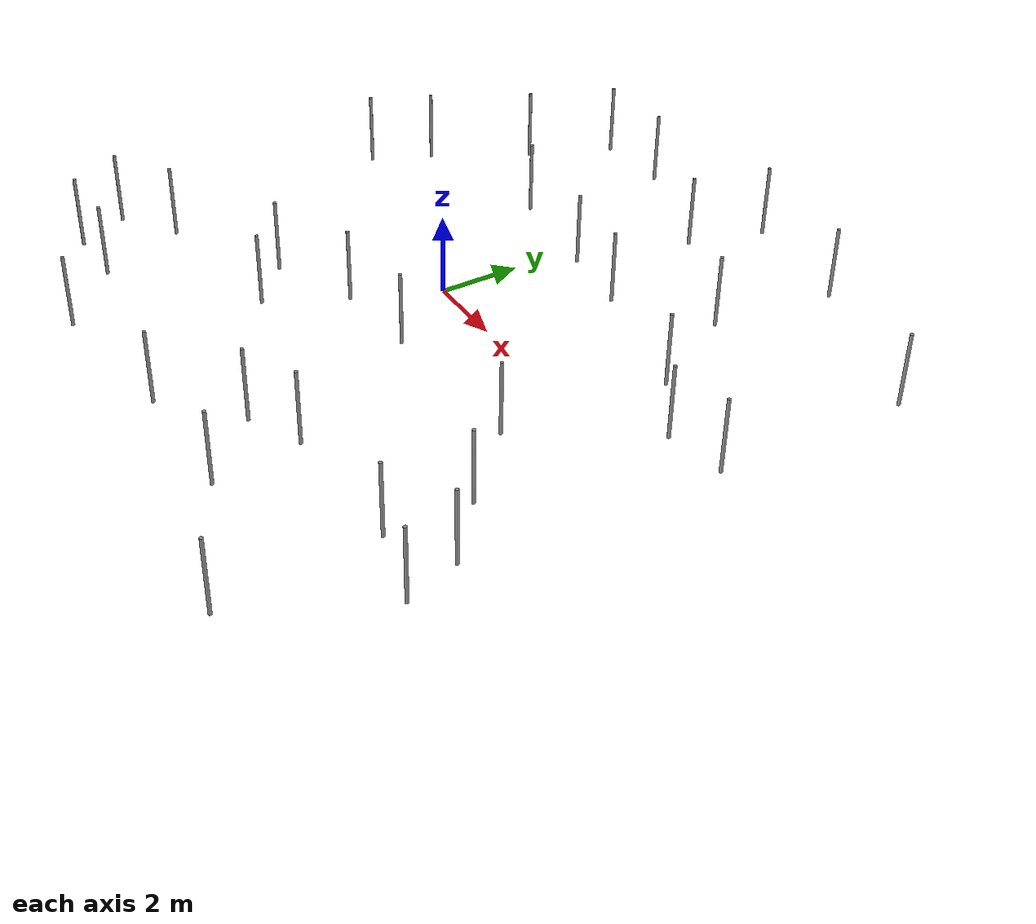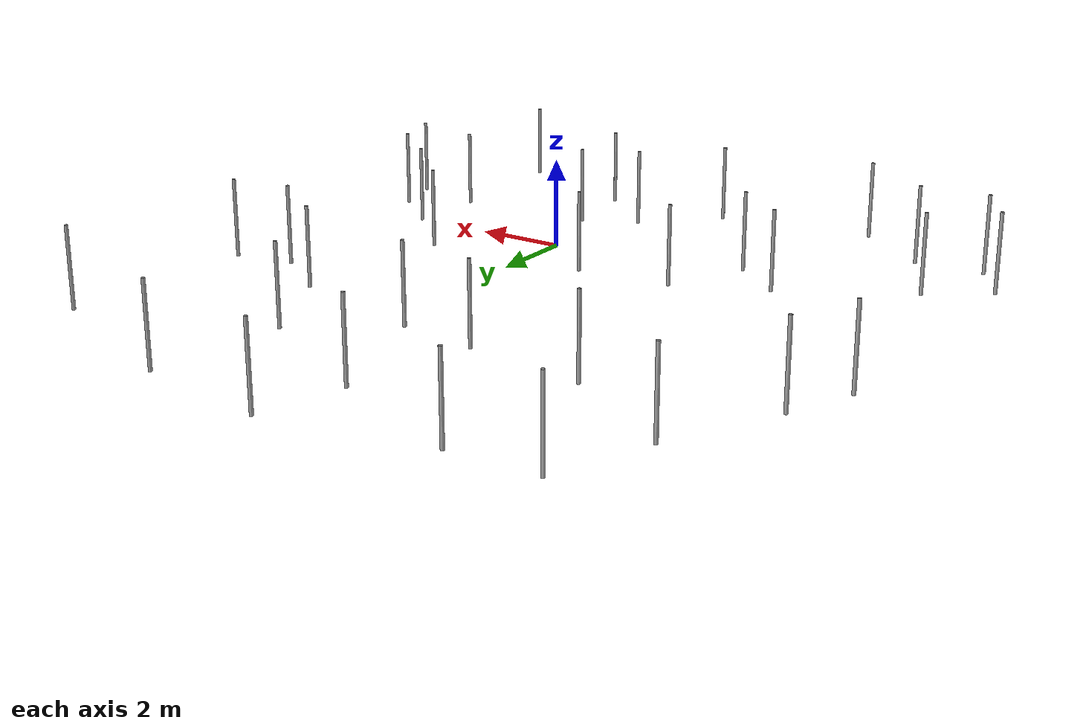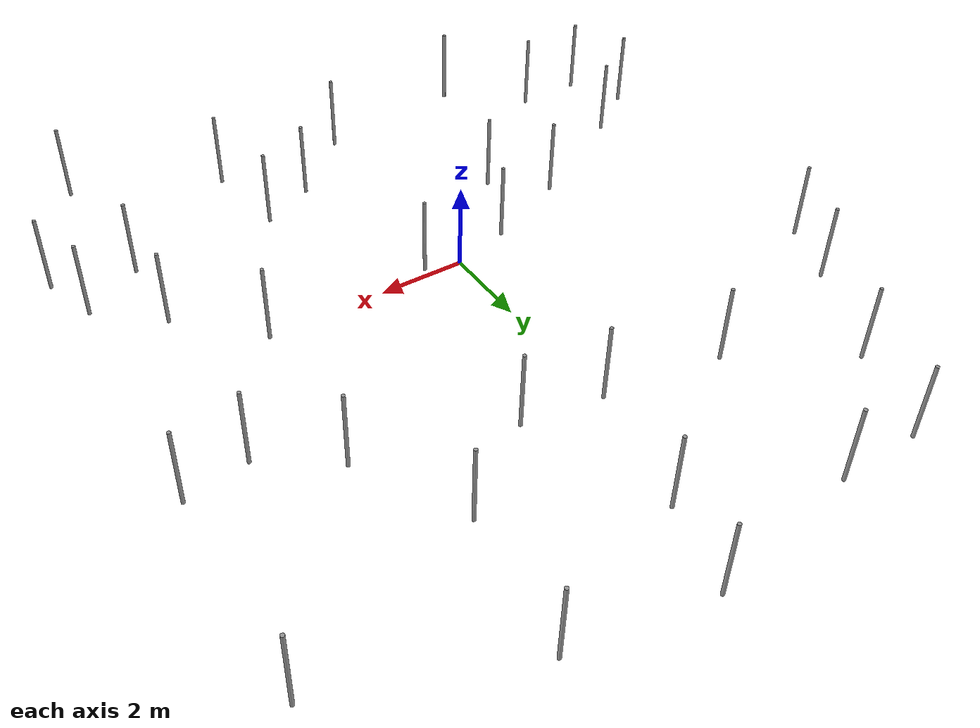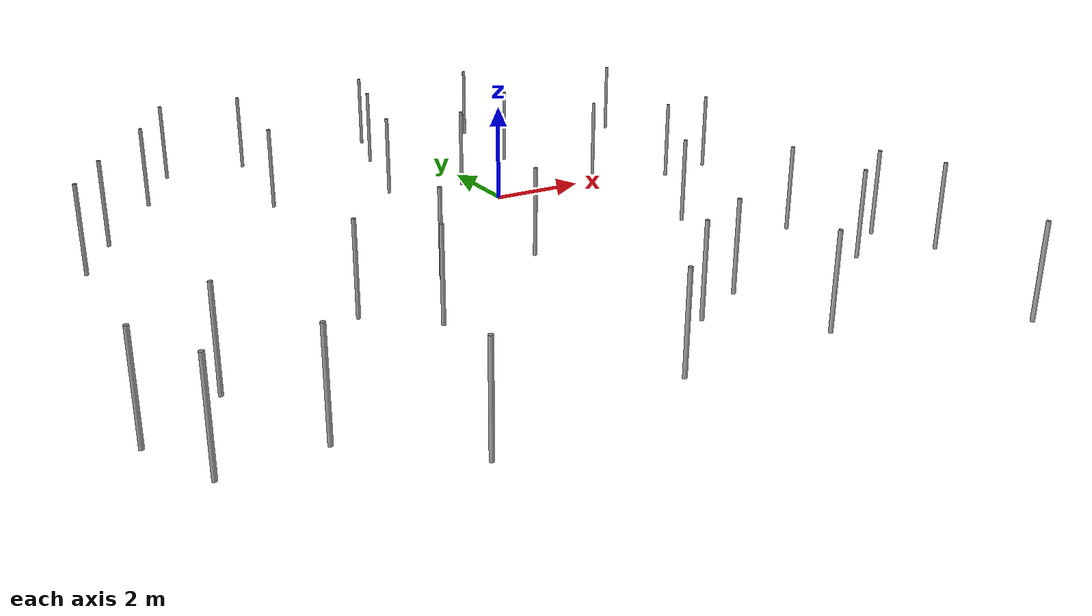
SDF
<?xml version='1.0'?>
<sdf version='1.7'>
  <model name='Complex1'>
    <link name='link_0'>
      <inertial>
        <mass>0.0136479</mass>
        <inertia>
          <ixx>0.00424334</ixx>
          <ixy>0</ixy>
          <ixz>0</ixz>
          <iyy>0.00424334</iyy>
          <iyz>0</iyz>
          <izz>1.17941e-05</izz>
        </inertia>
        <pose>0 0 0 0 -0 0</pose>
      </inertial>
      <pose>4.65489 3.18939 0 0 -0 0</pose>
      <visual name='visual'>
        <pose>0 0 0 0 -0 0</pose>
        <geometry>
          <cylinder>
            <radius>0.0415732</radius>
            <length>1.93023</length>
          </cylinder>
        </geometry>
        <material>
          <lighting>1</lighting>
          <script>
            <uri>file://media/materials/scripts/gazebo.material</uri>
            <name>Gazebo/Grey</name>
          </script>
          <shader type='pixel'/>
        </material>
        <transparency>0</transparency>
        <cast_shadows>1</cast_shadows>
      </visual>
      <collision name='collision'>
        <laser_retro>0</laser_retro>
        <max_contacts>10</max_contacts>
        <pose>0 0 0 0 -0 0</pose>
        <geometry>
          <cylinder>
            <radius>0.041573</radius>
            <length>1.93023</length>
          </cylinder>
        </geometry>
        <surface>
          <friction>
            <ode>
              <mu>1</mu>
              <mu2>1</mu2>
              <fdir1>0 0 0</fdir1>
              <slip1>0</slip1>
              <slip2>0</slip2>
            </ode>
            <torsional>
              <coefficient>1</coefficient>
              <patch_radius>0</patch_radius>
              <surface_radius>0</surface_radius>
              <use_patch_radius>1</use_patch_radius>
              <ode>
                <slip>0</slip>
              </ode>
            </torsional>
          </friction>
          <bounce>
            <restitution_coefficient>0</restitution_coefficient>
            <threshold>1e+06</threshold>
          </bounce>
          <contact>
            <collide_without_contact>0</collide_without_contact>
            <collide_without_contact_bitmask>1</collide_without_contact_bitmask>
            <collide_bitmask>1</collide_bitmask>
            <ode>
              <soft_cfm>0</soft_cfm>
              <soft_erp>0.2</soft_erp>
              <kp>1e+13</kp>
              <kd>1</kd>
              <max_vel>0.01</max_vel>
              <min_depth>0</min_depth>
            </ode>
            <bullet>
              <split_impulse>1</split_impulse>
              <split_impulse_penetration_threshold>-0.01</split_impulse_penetration_threshold>
              <soft_cfm>0</soft_cfm>
              <soft_erp>0.2</soft_erp>
              <kp>1e+13</kp>
              <kd>1</kd>
            </bullet>
          </contact>
        </surface>
      </collision>
    </link>
    <link name='link_0_clone'>
      <inertial>
        <mass>0.0136479</mass>
        <inertia>
          <ixx>0.00424334</ixx>
          <ixy>0</ixy>
          <ixz>0</ixz>
          <iyy>0.00424334</iyy>
          <iyz>0</iyz>
          <izz>1.17941e-05</izz>
        </inertia>
        <pose>0 0 0 0 -0 0</pose>
      </inertial>
      <pose>4.31703 -1.02058 0 0 -0 0</pose>
      <visual name='visual'>
        <pose>0 0 0 0 -0 0</pose>
        <geometry>
          <cylinder>
            <radius>0.0415732</radius>
            <length>1.93023</length>
          </cylinder>
        </geometry>
        <material>
          <lighting>1</lighting>
          <script>
            <uri>file://media/materials/scripts/gazebo.material</uri>
            <name>Gazebo/Grey</name>
          </script>
          <shader type='pixel'/>
        </material>
        <transparency>0</transparency>
        <cast_shadows>1</cast_shadows>
      </visual>
      <collision name='collision'>
        <laser_retro>0</laser_retro>
        <max_contacts>10</max_contacts>
        <pose>0 0 0 0 -0 0</pose>
        <geometry>
          <cylinder>
            <radius>0.041573</radius>
            <length>1.93023</length>
          </cylinder>
        </geometry>
        <surface>
          <friction>
            <ode>
              <mu>1</mu>
              <mu2>1</mu2>
              <fdir1>0 0 0</fdir1>
              <slip1>0</slip1>
              <slip2>0</slip2>
            </ode>
            <torsional>
              <coefficient>1</coefficient>
              <patch_radius>0</patch_radius>
              <surface_radius>0</surface_radius>
              <use_patch_radius>1</use_patch_radius>
              <ode>
                <slip>0</slip>
              </ode>
            </torsional>
          </friction>
          <bounce>
            <restitution_coefficient>0</restitution_coefficient>
            <threshold>1e+06</threshold>
          </bounce>
          <contact>
            <collide_without_contact>0</collide_without_contact>
            <collide_without_contact_bitmask>1</collide_without_contact_bitmask>
            <collide_bitmask>1</collide_bitmask>
            <ode>
              <soft_cfm>0</soft_cfm>
              <soft_erp>0.2</soft_erp>
              <kp>1e+13</kp>
              <kd>1</kd>
              <max_vel>0.01</max_vel>
              <min_depth>0</min_depth>
            </ode>
            <bullet>
              <split_impulse>1</split_impulse>
              <split_impulse_penetration_threshold>-0.01</split_impulse_penetration_threshold>
              <soft_cfm>0</soft_cfm>
              <soft_erp>0.2</soft_erp>
              <kp>1e+13</kp>
              <kd>1</kd>
            </bullet>
          </contact>
        </surface>
      </collision>
    </link>
    <link name='link_0_clone_clone'>
      <inertial>
        <mass>0.0136479</mass>
        <inertia>
          <ixx>0.00424334</ixx>
          <ixy>0</ixy>
          <ixz>0</ixz>
          <iyy>0.00424334</iyy>
          <iyz>0</iyz>
          <izz>1.17941e-05</izz>
        </inertia>
        <pose>0 0 0 0 -0 0</pose>
      </inertial>
      <pose>1.16618 4.08701 0 0 -0 0</pose>
      <visual name='visual'>
        <pose>0 0 0 0 -0 0</pose>
        <geometry>
          <cylinder>
            <radius>0.0415732</radius>
            <length>1.93023</length>
          </cylinder>
        </geometry>
        <material>
          <lighting>1</lighting>
          <script>
            <uri>file://media/materials/scripts/gazebo.material</uri>
            <name>Gazebo/Grey</name>
          </script>
          <shader type='pixel'/>
        </material>
        <transparency>0</transparency>
        <cast_shadows>1</cast_shadows>
      </visual>
      <collision name='collision'>
        <laser_retro>0</laser_retro>
        <max_contacts>10</max_contacts>
        <pose>0 0 0 0 -0 0</pose>
        <geometry>
          <cylinder>
            <radius>0.041573</radius>
            <length>1.93023</length>
          </cylinder>
        </geometry>
        <surface>
          <friction>
            <ode>
              <mu>1</mu>
              <mu2>1</mu2>
              <fdir1>0 0 0</fdir1>
              <slip1>0</slip1>
              <slip2>0</slip2>
            </ode>
            <torsional>
              <coefficient>1</coefficient>
              <patch_radius>0</patch_radius>
              <surface_radius>0</surface_radius>
              <use_patch_radius>1</use_patch_radius>
              <ode>
                <slip>0</slip>
              </ode>
            </torsional>
          </friction>
          <bounce>
            <restitution_coefficient>0</restitution_coefficient>
            <threshold>1e+06</threshold>
          </bounce>
          <contact>
            <collide_without_contact>0</collide_without_contact>
            <collide_without_contact_bitmask>1</collide_without_contact_bitmask>
            <collide_bitmask>1</collide_bitmask>
            <ode>
              <soft_cfm>0</soft_cfm>
              <soft_erp>0.2</soft_erp>
              <kp>1e+13</kp>
              <kd>1</kd>
              <max_vel>0.01</max_vel>
              <min_depth>0</min_depth>
            </ode>
            <bullet>
              <split_impulse>1</split_impulse>
              <split_impulse_penetration_threshold>-0.01</split_impulse_penetration_threshold>
              <soft_cfm>0</soft_cfm>
              <soft_erp>0.2</soft_erp>
              <kp>1e+13</kp>
              <kd>1</kd>
            </bullet>
          </contact>
        </surface>
      </collision>
    </link>
    <link name='link_0_clone_clone_0'>
      <inertial>
        <mass>0.0136479</mass>
        <inertia>
          <ixx>0.00424334</ixx>
          <ixy>0</ixy>
          <ixz>0</ixz>
          <iyy>0.00424334</iyy>
          <iyz>0</iyz>
          <izz>1.17941e-05</izz>
        </inertia>
        <pose>0 0 0 0 -0 0</pose>
      </inertial>
      <pose>-0.758174 4.35113 0 0 -0 0</pose>
      <visual name='visual'>
        <pose>0 0 0 0 -0 0</pose>
        <geometry>
          <cylinder>
            <radius>0.0415732</radius>
            <length>1.93023</length>
          </cylinder>
        </geometry>
        <material>
          <lighting>1</lighting>
          <script>
            <uri>file://media/materials/scripts/gazebo.material</uri>
            <name>Gazebo/Grey</name>
          </script>
          <shader type='pixel'/>
        </material>
        <transparency>0</transparency>
        <cast_shadows>1</cast_shadows>
      </visual>
      <collision name='collision'>
        <laser_retro>0</laser_retro>
        <max_contacts>10</max_contacts>
        <pose>0 0 0 0 -0 0</pose>
        <geometry>
          <cylinder>
            <radius>0.041573</radius>
            <length>1.93023</length>
          </cylinder>
        </geometry>
        <surface>
          <friction>
            <ode>
              <mu>1</mu>
              <mu2>1</mu2>
              <fdir1>0 0 0</fdir1>
              <slip1>0</slip1>
              <slip2>0</slip2>
            </ode>
            <torsional>
              <coefficient>1</coefficient>
              <patch_radius>0</patch_radius>
              <surface_radius>0</surface_radius>
              <use_patch_radius>1</use_patch_radius>
              <ode>
                <slip>0</slip>
              </ode>
            </torsional>
          </friction>
          <bounce>
            <restitution_coefficient>0</restitution_coefficient>
            <threshold>1e+06</threshold>
          </bounce>
          <contact>
            <collide_without_contact>0</collide_without_contact>
            <collide_without_contact_bitmask>1</collide_without_contact_bitmask>
            <collide_bitmask>1</collide_bitmask>
            <ode>
              <soft_cfm>0</soft_cfm>
              <soft_erp>0.2</soft_erp>
              <kp>1e+13</kp>
              <kd>1</kd>
              <max_vel>0.01</max_vel>
              <min_depth>0</min_depth>
            </ode>
            <bullet>
              <split_impulse>1</split_impulse>
              <split_impulse_penetration_threshold>-0.01</split_impulse_penetration_threshold>
              <soft_cfm>0</soft_cfm>
              <soft_erp>0.2</soft_erp>
              <kp>1e+13</kp>
              <kd>1</kd>
            </bullet>
          </contact>
        </surface>
      </collision>
    </link>
    <link name='link_0_clone_clone_1'>
      <inertial>
        <mass>0.0136479</mass>
        <inertia>
          <ixx>0.00424334</ixx>
          <ixy>0</ixy>
          <ixz>0</ixz>
          <iyy>0.00424334</iyy>
          <iyz>0</iyz>
          <izz>1.17941e-05</izz>
        </inertia>
        <pose>0 0 0 0 -0 0</pose>
      </inertial>
      <pose>-0.04092 7.35716 0 0 -0 0</pose>
      <visual name='visual'>
        <pose>0 0 0 0 -0 0</pose>
        <geometry>
          <cylinder>
            <radius>0.0415732</radius>
            <length>1.93023</length>
          </cylinder>
        </geometry>
        <material>
          <lighting>1</lighting>
          <script>
            <uri>file://media/materials/scripts/gazebo.material</uri>
            <name>Gazebo/Grey</name>
          </script>
          <shader type='pixel'/>
        </material>
        <transparency>0</transparency>
        <cast_shadows>1</cast_shadows>
      </visual>
      <collision name='collision'>
        <laser_retro>0</laser_retro>
        <max_contacts>10</max_contacts>
        <pose>0 0 0 0 -0 0</pose>
        <geometry>
          <cylinder>
            <radius>0.041573</radius>
            <length>1.93023</length>
          </cylinder>
        </geometry>
        <surface>
          <friction>
            <ode>
              <mu>1</mu>
              <mu2>1</mu2>
              <fdir1>0 0 0</fdir1>
              <slip1>0</slip1>
              <slip2>0</slip2>
            </ode>
            <torsional>
              <coefficient>1</coefficient>
              <patch_radius>0</patch_radius>
              <surface_radius>0</surface_radius>
              <use_patch_radius>1</use_patch_radius>
              <ode>
                <slip>0</slip>
              </ode>
            </torsional>
          </friction>
          <bounce>
            <restitution_coefficient>0</restitution_coefficient>
            <threshold>1e+06</threshold>
          </bounce>
          <contact>
            <collide_without_contact>0</collide_without_contact>
            <collide_without_contact_bitmask>1</collide_without_contact_bitmask>
            <collide_bitmask>1</collide_bitmask>
            <ode>
              <soft_cfm>0</soft_cfm>
              <soft_erp>0.2</soft_erp>
              <kp>1e+13</kp>
              <kd>1</kd>
              <max_vel>0.01</max_vel>
              <min_depth>0</min_depth>
            </ode>
            <bullet>
              <split_impulse>1</split_impulse>
              <split_impulse_penetration_threshold>-0.01</split_impulse_penetration_threshold>
              <soft_cfm>0</soft_cfm>
              <soft_erp>0.2</soft_erp>
              <kp>1e+13</kp>
              <kd>1</kd>
            </bullet>
          </contact>
        </surface>
      </collision>
    </link>
    <link name='link_0_clone_clone_10'>
      <inertial>
        <mass>0.0136479</mass>
        <inertia>
          <ixx>0.00424334</ixx>
          <ixy>0</ixy>
          <ixz>0</ixz>
          <iyy>0.00424334</iyy>
          <iyz>0</iyz>
          <izz>1.17941e-05</izz>
        </inertia>
        <pose>0 0 0 0 -0 0</pose>
      </inertial>
      <pose>7.76019 2.34724 0 0 -0 0</pose>
      <visual name='visual'>
        <pose>0 0 0 0 -0 0</pose>
        <geometry>
          <cylinder>
            <radius>0.0415732</radius>
            <length>1.93023</length>
          </cylinder>
        </geometry>
        <material>
          <lighting>1</lighting>
          <script>
            <uri>file://media/materials/scripts/gazebo.material</uri>
            <name>Gazebo/Grey</name>
          </script>
          <shader type='pixel'/>
        </material>
        <transparency>0</transparency>
        <cast_shadows>1</cast_shadows>
      </visual>
      <collision name='collision'>
        <laser_retro>0</laser_retro>
        <max_contacts>10</max_contacts>
        <pose>0 0 0 0 -0 0</pose>
        <geometry>
          <cylinder>
            <radius>0.041573</radius>
            <length>1.93023</length>
          </cylinder>
        </geometry>
        <surface>
          <friction>
            <ode>
              <mu>1</mu>
              <mu2>1</mu2>
              <fdir1>0 0 0</fdir1>
              <slip1>0</slip1>
              <slip2>0</slip2>
            </ode>
            <torsional>
              <coefficient>1</coefficient>
              <patch_radius>0</patch_radius>
              <surface_radius>0</surface_radius>
              <use_patch_radius>1</use_patch_radius>
              <ode>
                <slip>0</slip>
              </ode>
            </torsional>
          </friction>
          <bounce>
            <restitution_coefficient>0</restitution_coefficient>
            <threshold>1e+06</threshold>
          </bounce>
          <contact>
            <collide_without_contact>0</collide_without_contact>
            <collide_without_contact_bitmask>1</collide_without_contact_bitmask>
            <collide_bitmask>1</collide_bitmask>
            <ode>
              <soft_cfm>0</soft_cfm>
              <soft_erp>0.2</soft_erp>
              <kp>1e+13</kp>
              <kd>1</kd>
              <max_vel>0.01</max_vel>
              <min_depth>0</min_depth>
            </ode>
            <bullet>
              <split_impulse>1</split_impulse>
              <split_impulse_penetration_threshold>-0.01</split_impulse_penetration_threshold>
              <soft_cfm>0</soft_cfm>
              <soft_erp>0.2</soft_erp>
              <kp>1e+13</kp>
              <kd>1</kd>
            </bullet>
          </contact>
        </surface>
      </collision>
    </link>
    <link name='link_0_clone_clone_11'>
      <inertial>
        <mass>0.0136479</mass>
        <inertia>
          <ixx>0.00424334</ixx>
          <ixy>0</ixy>
          <ixz>0</ixz>
          <iyy>0.00424334</iyy>
          <iyz>0</iyz>
          <izz>1.17941e-05</izz>
        </inertia>
        <pose>0 0 0 0 -0 0</pose>
      </inertial>
      <pose>6.26362 2.0826 0 0 -0 0</pose>
      <visual name='visual'>
        <pose>0 0 0 0 -0 0</pose>
        <geometry>
          <cylinder>
            <radius>0.0415732</radius>
            <length>1.93023</length>
          </cylinder>
        </geometry>
        <material>
          <lighting>1</lighting>
          <script>
            <uri>file://media/materials/scripts/gazebo.material</uri>
            <name>Gazebo/Grey</name>
          </script>
          <shader type='pixel'/>
        </material>
        <transparency>0</transparency>
        <cast_shadows>1</cast_shadows>
      </visual>
      <collision name='collision'>
        <laser_retro>0</laser_retro>
        <max_contacts>10</max_contacts>
        <pose>0 0 0 0 -0 0</pose>
        <geometry>
          <cylinder>
            <radius>0.041573</radius>
            <length>1.93023</length>
          </cylinder>
        </geometry>
        <surface>
          <friction>
            <ode>
              <mu>1</mu>
              <mu2>1</mu2>
              <fdir1>0 0 0</fdir1>
              <slip1>0</slip1>
              <slip2>0</slip2>
            </ode>
            <torsional>
              <coefficient>1</coefficient>
              <patch_radius>0</patch_radius>
              <surface_radius>0</surface_radius>
              <use_patch_radius>1</use_patch_radius>
              <ode>
                <slip>0</slip>
              </ode>
            </torsional>
          </friction>
          <bounce>
            <restitution_coefficient>0</restitution_coefficient>
            <threshold>1e+06</threshold>
          </bounce>
          <contact>
            <collide_without_contact>0</collide_without_contact>
            <collide_without_contact_bitmask>1</collide_without_contact_bitmask>
            <collide_bitmask>1</collide_bitmask>
            <ode>
              <soft_cfm>0</soft_cfm>
              <soft_erp>0.2</soft_erp>
              <kp>1e+13</kp>
              <kd>1</kd>
              <max_vel>0.01</max_vel>
              <min_depth>0</min_depth>
            </ode>
            <bullet>
              <split_impulse>1</split_impulse>
              <split_impulse_penetration_threshold>-0.01</split_impulse_penetration_threshold>
              <soft_cfm>0</soft_cfm>
              <soft_erp>0.2</soft_erp>
              <kp>1e+13</kp>
              <kd>1</kd>
            </bullet>
          </contact>
        </surface>
      </collision>
    </link>
    <link name='link_0_clone_clone_12'>
      <inertial>
        <mass>0.0136479</mass>
        <inertia>
          <ixx>0.00424334</ixx>
          <ixy>0</ixy>
          <ixz>0</ixz>
          <iyy>0.00424334</iyy>
          <iyz>0</iyz>
          <izz>1.17941e-05</izz>
        </inertia>
        <pose>0 0 0 0 -0 0</pose>
      </inertial>
      <pose>7.90087 7.24069 0 0 -0 0</pose>
      <visual name='visual'>
        <pose>0 0 0 0 -0 0</pose>
        <geometry>
          <cylinder>
            <radius>0.0415732</radius>
            <length>1.93023</length>
          </cylinder>
        </geometry>
        <material>
          <lighting>1</lighting>
          <script>
            <uri>file://media/materials/scripts/gazebo.material</uri>
            <name>Gazebo/Grey</name>
          </script>
          <shader type='pixel'/>
        </material>
        <transparency>0</transparency>
        <cast_shadows>1</cast_shadows>
      </visual>
      <collision name='collision'>
        <laser_retro>0</laser_retro>
        <max_contacts>10</max_contacts>
        <pose>0 0 0 0 -0 0</pose>
        <geometry>
          <cylinder>
            <radius>0.041573</radius>
            <length>1.93023</length>
          </cylinder>
        </geometry>
        <surface>
          <friction>
            <ode>
              <mu>1</mu>
              <mu2>1</mu2>
              <fdir1>0 0 0</fdir1>
              <slip1>0</slip1>
              <slip2>0</slip2>
            </ode>
            <torsional>
              <coefficient>1</coefficient>
              <patch_radius>0</patch_radius>
              <surface_radius>0</surface_radius>
              <use_patch_radius>1</use_patch_radius>
              <ode>
                <slip>0</slip>
              </ode>
            </torsional>
          </friction>
          <bounce>
            <restitution_coefficient>0</restitution_coefficient>
            <threshold>1e+06</threshold>
          </bounce>
          <contact>
            <collide_without_contact>0</collide_without_contact>
            <collide_without_contact_bitmask>1</collide_without_contact_bitmask>
            <collide_bitmask>1</collide_bitmask>
            <ode>
              <soft_cfm>0</soft_cfm>
              <soft_erp>0.2</soft_erp>
              <kp>1e+13</kp>
              <kd>1</kd>
              <max_vel>0.01</max_vel>
              <min_depth>0</min_depth>
            </ode>
            <bullet>
              <split_impulse>1</split_impulse>
              <split_impulse_penetration_threshold>-0.01</split_impulse_penetration_threshold>
              <soft_cfm>0</soft_cfm>
              <soft_erp>0.2</soft_erp>
              <kp>1e+13</kp>
              <kd>1</kd>
            </bullet>
          </contact>
        </surface>
      </collision>
    </link>
    <link name='link_0_clone_clone_13'>
      <inertial>
        <mass>0.0136479</mass>
        <inertia>
          <ixx>0.00424334</ixx>
          <ixy>0</ixy>
          <ixz>0</ixz>
          <iyy>0.00424334</iyy>
          <iyz>0</iyz>
          <izz>1.17941e-05</izz>
        </inertia>
        <pose>0 0 0 0 -0 0</pose>
      </inertial>
      <pose>3.71056 8.85119 0 0 -0 0</pose>
      <visual name='visual'>
        <pose>0 0 0 0 -0 0</pose>
        <geometry>
          <cylinder>
            <radius>0.0415732</radius>
            <length>1.93023</length>
          </cylinder>
        </geometry>
        <material>
          <lighting>1</lighting>
          <script>
            <uri>file://media/materials/scripts/gazebo.material</uri>
            <name>Gazebo/Grey</name>
          </script>
          <shader type='pixel'/>
        </material>
        <transparency>0</transparency>
        <cast_shadows>1</cast_shadows>
      </visual>
      <collision name='collision'>
        <laser_retro>0</laser_retro>
        <max_contacts>10</max_contacts>
        <pose>0 0 0 0 -0 0</pose>
        <geometry>
          <cylinder>
            <radius>0.041573</radius>
            <length>1.93023</length>
          </cylinder>
        </geometry>
        <surface>
          <friction>
            <ode>
              <mu>1</mu>
              <mu2>1</mu2>
              <fdir1>0 0 0</fdir1>
              <slip1>0</slip1>
              <slip2>0</slip2>
            </ode>
            <torsional>
              <coefficient>1</coefficient>
              <patch_radius>0</patch_radius>
              <surface_radius>0</surface_radius>
              <use_patch_radius>1</use_patch_radius>
              <ode>
                <slip>0</slip>
              </ode>
            </torsional>
          </friction>
          <bounce>
            <restitution_coefficient>0</restitution_coefficient>
            <threshold>1e+06</threshold>
          </bounce>
          <contact>
            <collide_without_contact>0</collide_without_contact>
            <collide_without_contact_bitmask>1</collide_without_contact_bitmask>
            <collide_bitmask>1</collide_bitmask>
            <ode>
              <soft_cfm>0</soft_cfm>
              <soft_erp>0.2</soft_erp>
              <kp>1e+13</kp>
              <kd>1</kd>
              <max_vel>0.01</max_vel>
              <min_depth>0</min_depth>
            </ode>
            <bullet>
              <split_impulse>1</split_impulse>
              <split_impulse_penetration_threshold>-0.01</split_impulse_penetration_threshold>
              <soft_cfm>0</soft_cfm>
              <soft_erp>0.2</soft_erp>
              <kp>1e+13</kp>
              <kd>1</kd>
            </bullet>
          </contact>
        </surface>
      </collision>
    </link>
    <link name='link_0_clone_clone_14'>
      <inertial>
        <mass>0.0136479</mass>
        <inertia>
          <ixx>0.00424334</ixx>
          <ixy>0</ixy>
          <ixz>0</ixz>
          <iyy>0.00424334</iyy>
          <iyz>0</iyz>
          <izz>1.17941e-05</izz>
        </inertia>
        <pose>0 0 0 0 -0 0</pose>
      </inertial>
      <pose>0.506588 9.34918 0 0 -0 0</pose>
      <visual name='visual'>
        <pose>0 0 0 0 -0 0</pose>
        <geometry>
          <cylinder>
            <radius>0.0415732</radius>
            <length>1.93023</length>
          </cylinder>
        </geometry>
        <material>
          <lighting>1</lighting>
          <script>
            <uri>file://media/materials/scripts/gazebo.material</uri>
            <name>Gazebo/Grey</name>
          </script>
          <shader type='pixel'/>
        </material>
        <transparency>0</transparency>
        <cast_shadows>1</cast_shadows>
      </visual>
      <collision name='collision'>
        <laser_retro>0</laser_retro>
        <max_contacts>10</max_contacts>
        <pose>0 0 0 0 -0 0</pose>
        <geometry>
          <cylinder>
            <radius>0.041573</radius>
            <length>1.93023</length>
          </cylinder>
        </geometry>
        <surface>
          <friction>
            <ode>
              <mu>1</mu>
              <mu2>1</mu2>
              <fdir1>0 0 0</fdir1>
              <slip1>0</slip1>
              <slip2>0</slip2>
            </ode>
            <torsional>
              <coefficient>1</coefficient>
              <patch_radius>0</patch_radius>
              <surface_radius>0</surface_radius>
              <use_patch_radius>1</use_patch_radius>
              <ode>
                <slip>0</slip>
              </ode>
            </torsional>
          </friction>
          <bounce>
            <restitution_coefficient>0</restitution_coefficient>
            <threshold>1e+06</threshold>
          </bounce>
          <contact>
            <collide_without_contact>0</collide_without_contact>
            <collide_without_contact_bitmask>1</collide_without_contact_bitmask>
            <collide_bitmask>1</collide_bitmask>
            <ode>
              <soft_cfm>0</soft_cfm>
              <soft_erp>0.2</soft_erp>
              <kp>1e+13</kp>
              <kd>1</kd>
              <max_vel>0.01</max_vel>
              <min_depth>0</min_depth>
            </ode>
            <bullet>
              <split_impulse>1</split_impulse>
              <split_impulse_penetration_threshold>-0.01</split_impulse_penetration_threshold>
              <soft_cfm>0</soft_cfm>
              <soft_erp>0.2</soft_erp>
              <kp>1e+13</kp>
              <kd>1</kd>
            </bullet>
          </contact>
        </surface>
      </collision>
    </link>
    <link name='link_0_clone_clone_15'>
      <inertial>
        <mass>0.0136479</mass>
        <inertia>
          <ixx>0.00424334</ixx>
          <ixy>0</ixy>
          <ixz>0</ixz>
          <iyy>0.00424334</iyy>
          <iyz>0</iyz>
          <izz>1.17941e-05</izz>
        </inertia>
        <pose>0 0 0 0 -0 0</pose>
      </inertial>
      <pose>-3.29555 8.61055 0 0 -0 0</pose>
      <visual name='visual'>
        <pose>0 0 0 0 -0 0</pose>
        <geometry>
          <cylinder>
            <radius>0.0415732</radius>
            <length>1.93023</length>
          </cylinder>
        </geometry>
        <material>
          <lighting>1</lighting>
          <script>
            <uri>file://media/materials/scripts/gazebo.material</uri>
            <name>Gazebo/Grey</name>
          </script>
          <shader type='pixel'/>
        </material>
        <transparency>0</transparency>
        <cast_shadows>1</cast_shadows>
      </visual>
      <collision name='collision'>
        <laser_retro>0</laser_retro>
        <max_contacts>10</max_contacts>
        <pose>0 0 0 0 -0 0</pose>
        <geometry>
          <cylinder>
            <radius>0.041573</radius>
            <length>1.93023</length>
          </cylinder>
        </geometry>
        <surface>
          <friction>
            <ode>
              <mu>1</mu>
              <mu2>1</mu2>
              <fdir1>0 0 0</fdir1>
              <slip1>0</slip1>
              <slip2>0</slip2>
            </ode>
            <torsional>
              <coefficient>1</coefficient>
              <patch_radius>0</patch_radius>
              <surface_radius>0</surface_radius>
              <use_patch_radius>1</use_patch_radius>
              <ode>
                <slip>0</slip>
              </ode>
            </torsional>
          </friction>
          <bounce>
            <restitution_coefficient>0</restitution_coefficient>
            <threshold>1e+06</threshold>
          </bounce>
          <contact>
            <collide_without_contact>0</collide_without_contact>
            <collide_without_contact_bitmask>1</collide_without_contact_bitmask>
            <collide_bitmask>1</collide_bitmask>
            <ode>
              <soft_cfm>0</soft_cfm>
              <soft_erp>0.2</soft_erp>
              <kp>1e+13</kp>
              <kd>1</kd>
              <max_vel>0.01</max_vel>
              <min_depth>0</min_depth>
            </ode>
            <bullet>
              <split_impulse>1</split_impulse>
              <split_impulse_penetration_threshold>-0.01</split_impulse_penetration_threshold>
              <soft_cfm>0</soft_cfm>
              <soft_erp>0.2</soft_erp>
              <kp>1e+13</kp>
              <kd>1</kd>
            </bullet>
          </contact>
        </surface>
      </collision>
    </link>
    <link name='link_0_clone_clone_16'>
      <inertial>
        <mass>0.0136479</mass>
        <inertia>
          <ixx>0.00424334</ixx>
          <ixy>0</ixy>
          <ixz>0</ixz>
          <iyy>0.00424334</iyy>
          <iyz>0</iyz>
          <izz>1.17941e-05</izz>
        </inertia>
        <pose>0 0 0 0 -0 0</pose>
      </inertial>
      <pose>-5.33458 8.53709 0 0 -0 0</pose>
      <visual name='visual'>
        <pose>0 0 0 0 -0 0</pose>
        <geometry>
          <cylinder>
            <radius>0.0415732</radius>
            <length>1.93023</length>
          </cylinder>
        </geometry>
        <material>
          <lighting>1</lighting>
          <script>
            <uri>file://media/materials/scripts/gazebo.material</uri>
            <name>Gazebo/Grey</name>
          </script>
          <shader type='pixel'/>
        </material>
        <transparency>0</transparency>
        <cast_shadows>1</cast_shadows>
      </visual>
      <collision name='collision'>
        <laser_retro>0</laser_retro>
        <max_contacts>10</max_contacts>
        <pose>0 0 0 0 -0 0</pose>
        <geometry>
          <cylinder>
            <radius>0.041573</radius>
            <length>1.93023</length>
          </cylinder>
        </geometry>
        <surface>
          <friction>
            <ode>
              <mu>1</mu>
              <mu2>1</mu2>
              <fdir1>0 0 0</fdir1>
              <slip1>0</slip1>
              <slip2>0</slip2>
            </ode>
            <torsional>
              <coefficient>1</coefficient>
              <patch_radius>0</patch_radius>
              <surface_radius>0</surface_radius>
              <use_patch_radius>1</use_patch_radius>
              <ode>
                <slip>0</slip>
              </ode>
            </torsional>
          </friction>
          <bounce>
            <restitution_coefficient>0</restitution_coefficient>
            <threshold>1e+06</threshold>
          </bounce>
          <contact>
            <collide_without_contact>0</collide_without_contact>
            <collide_without_contact_bitmask>1</collide_without_contact_bitmask>
            <collide_bitmask>1</collide_bitmask>
            <ode>
              <soft_cfm>0</soft_cfm>
              <soft_erp>0.2</soft_erp>
              <kp>1e+13</kp>
              <kd>1</kd>
              <max_vel>0.01</max_vel>
              <min_depth>0</min_depth>
            </ode>
            <bullet>
              <split_impulse>1</split_impulse>
              <split_impulse_penetration_threshold>-0.01</split_impulse_penetration_threshold>
              <soft_cfm>0</soft_cfm>
              <soft_erp>0.2</soft_erp>
              <kp>1e+13</kp>
              <kd>1</kd>
            </bullet>
          </contact>
        </surface>
      </collision>
    </link>
    <link name='link_0_clone_clone_17'>
      <inertial>
        <mass>0.0136479</mass>
        <inertia>
          <ixx>0.00424334</ixx>
          <ixy>0</ixy>
          <ixz>0</ixz>
          <iyy>0.00424334</iyy>
          <iyz>0</iyz>
          <izz>1.17941e-05</izz>
        </inertia>
        <pose>0 0 0 0 -0 0</pose>
      </inertial>
      <pose>-6.23981 6.34724 0 0 -0 0</pose>
      <visual name='visual'>
        <pose>0 0 0 0 -0 0</pose>
        <geometry>
          <cylinder>
            <radius>0.0415732</radius>
            <length>1.93023</length>
          </cylinder>
        </geometry>
        <material>
          <lighting>1</lighting>
          <script>
            <uri>file://media/materials/scripts/gazebo.material</uri>
            <name>Gazebo/Grey</name>
          </script>
          <shader type='pixel'/>
        </material>
        <transparency>0</transparency>
        <cast_shadows>1</cast_shadows>
      </visual>
      <collision name='collision'>
        <laser_retro>0</laser_retro>
        <max_contacts>10</max_contacts>
        <pose>0 0 0 0 -0 0</pose>
        <geometry>
          <cylinder>
            <radius>0.041573</radius>
            <length>1.93023</length>
          </cylinder>
        </geometry>
        <surface>
          <friction>
            <ode>
              <mu>1</mu>
              <mu2>1</mu2>
              <fdir1>0 0 0</fdir1>
              <slip1>0</slip1>
              <slip2>0</slip2>
            </ode>
            <torsional>
              <coefficient>1</coefficient>
              <patch_radius>0</patch_radius>
              <surface_radius>0</surface_radius>
              <use_patch_radius>1</use_patch_radius>
              <ode>
                <slip>0</slip>
              </ode>
            </torsional>
          </friction>
          <bounce>
            <restitution_coefficient>0</restitution_coefficient>
            <threshold>1e+06</threshold>
          </bounce>
          <contact>
            <collide_without_contact>0</collide_without_contact>
            <collide_without_contact_bitmask>1</collide_without_contact_bitmask>
            <collide_bitmask>1</collide_bitmask>
            <ode>
              <soft_cfm>0</soft_cfm>
              <soft_erp>0.2</soft_erp>
              <kp>1e+13</kp>
              <kd>1</kd>
              <max_vel>0.01</max_vel>
              <min_depth>0</min_depth>
            </ode>
            <bullet>
              <split_impulse>1</split_impulse>
              <split_impulse_penetration_threshold>-0.01</split_impulse_penetration_threshold>
              <soft_cfm>0</soft_cfm>
              <soft_erp>0.2</soft_erp>
              <kp>1e+13</kp>
              <kd>1</kd>
            </bullet>
          </contact>
        </surface>
      </collision>
    </link>
    <link name='link_0_clone_clone_18'>
      <inertial>
        <mass>0.0136479</mass>
        <inertia>
          <ixx>0.00424334</ixx>
          <ixy>0</ixy>
          <ixz>0</ixz>
          <iyy>0.00424334</iyy>
          <iyz>0</iyz>
          <izz>1.17941e-05</izz>
        </inertia>
        <pose>0 0 0 0 -0 0</pose>
      </inertial>
      <pose>-3.62288 4.73882 0 0 -0 0</pose>
      <visual name='visual'>
        <pose>0 0 0 0 -0 0</pose>
        <geometry>
          <cylinder>
            <radius>0.0415732</radius>
            <length>1.93023</length>
          </cylinder>
        </geometry>
        <material>
          <lighting>1</lighting>
          <script>
            <uri>file://media/materials/scripts/gazebo.material</uri>
            <name>Gazebo/Grey</name>
          </script>
          <shader type='pixel'/>
        </material>
        <transparency>0</transparency>
        <cast_shadows>1</cast_shadows>
      </visual>
      <collision name='collision'>
        <laser_retro>0</laser_retro>
        <max_contacts>10</max_contacts>
        <pose>0 0 0 0 -0 0</pose>
        <geometry>
          <cylinder>
            <radius>0.041573</radius>
            <length>1.93023</length>
          </cylinder>
        </geometry>
        <surface>
          <friction>
            <ode>
              <mu>1</mu>
              <mu2>1</mu2>
              <fdir1>0 0 0</fdir1>
              <slip1>0</slip1>
              <slip2>0</slip2>
            </ode>
            <torsional>
              <coefficient>1</coefficient>
              <patch_radius>0</patch_radius>
              <surface_radius>0</surface_radius>
              <use_patch_radius>1</use_patch_radius>
              <ode>
                <slip>0</slip>
              </ode>
            </torsional>
          </friction>
          <bounce>
            <restitution_coefficient>0</restitution_coefficient>
            <threshold>1e+06</threshold>
          </bounce>
          <contact>
            <collide_without_contact>0</collide_without_contact>
            <collide_without_contact_bitmask>1</collide_without_contact_bitmask>
            <collide_bitmask>1</collide_bitmask>
            <ode>
              <soft_cfm>0</soft_cfm>
              <soft_erp>0.2</soft_erp>
              <kp>1e+13</kp>
              <kd>1</kd>
              <max_vel>0.01</max_vel>
              <min_depth>0</min_depth>
            </ode>
            <bullet>
              <split_impulse>1</split_impulse>
              <split_impulse_penetration_threshold>-0.01</split_impulse_penetration_threshold>
              <soft_cfm>0</soft_cfm>
              <soft_erp>0.2</soft_erp>
              <kp>1e+13</kp>
              <kd>1</kd>
            </bullet>
          </contact>
        </surface>
      </collision>
    </link>
    <link name='link_0_clone_clone_19'>
      <inertial>
        <mass>0.0136479</mass>
        <inertia>
          <ixx>0.00424334</ixx>
          <ixy>0</ixy>
          <ixz>0</ixz>
          <iyy>0.00424334</iyy>
          <iyz>0</iyz>
          <izz>1.17941e-05</izz>
        </inertia>
        <pose>0 0 0 0 -0 0</pose>
      </inertial>
      <pose>-8.23981 2.34724 0 0 -0 0</pose>
      <visual name='visual'>
        <pose>0 0 0 0 -0 0</pose>
        <geometry>
          <cylinder>
            <radius>0.0415732</radius>
            <length>1.93023</length>
          </cylinder>
        </geometry>
        <material>
          <lighting>1</lighting>
          <script>
            <uri>file://media/materials/scripts/gazebo.material</uri>
            <name>Gazebo/Grey</name>
          </script>
          <shader type='pixel'/>
        </material>
        <transparency>0</transparency>
        <cast_shadows>1</cast_shadows>
      </visual>
      <collision name='collision'>
        <laser_retro>0</laser_retro>
        <max_contacts>10</max_contacts>
        <pose>0 0 0 0 -0 0</pose>
        <geometry>
          <cylinder>
            <radius>0.041573</radius>
            <length>1.93023</length>
          </cylinder>
        </geometry>
        <surface>
          <friction>
            <ode>
              <mu>1</mu>
              <mu2>1</mu2>
              <fdir1>0 0 0</fdir1>
              <slip1>0</slip1>
              <slip2>0</slip2>
            </ode>
            <torsional>
              <coefficient>1</coefficient>
              <patch_radius>0</patch_radius>
              <surface_radius>0</surface_radius>
              <use_patch_radius>1</use_patch_radius>
              <ode>
                <slip>0</slip>
              </ode>
            </torsional>
          </friction>
          <bounce>
            <restitution_coefficient>0</restitution_coefficient>
            <threshold>1e+06</threshold>
          </bounce>
          <contact>
            <collide_without_contact>0</collide_without_contact>
            <collide_without_contact_bitmask>1</collide_without_contact_bitmask>
            <collide_bitmask>1</collide_bitmask>
            <ode>
              <soft_cfm>0</soft_cfm>
              <soft_erp>0.2</soft_erp>
              <kp>1e+13</kp>
              <kd>1</kd>
              <max_vel>0.01</max_vel>
              <min_depth>0</min_depth>
            </ode>
            <bullet>
              <split_impulse>1</split_impulse>
              <split_impulse_penetration_threshold>-0.01</split_impulse_penetration_threshold>
              <soft_cfm>0</soft_cfm>
              <soft_erp>0.2</soft_erp>
              <kp>1e+13</kp>
              <kd>1</kd>
            </bullet>
          </contact>
        </surface>
      </collision>
    </link>
    <link name='link_0_clone_clone_2'>
      <inertial>
        <mass>0.0136479</mass>
        <inertia>
          <ixx>0.00424334</ixx>
          <ixy>0</ixy>
          <ixz>0</ixz>
          <iyy>0.00424334</iyy>
          <iyz>0</iyz>
          <izz>1.17941e-05</izz>
        </inertia>
        <pose>0 0 0 0 -0 0</pose>
      </inertial>
      <pose>0.177265 -1.24651 0 0 -0 0</pose>
      <visual name='visual'>
        <pose>0 0 0 0 -0 0</pose>
        <geometry>
          <cylinder>
            <radius>0.0415732</radius>
            <length>1.93023</length>
          </cylinder>
        </geometry>
        <material>
          <lighting>1</lighting>
          <script>
            <uri>file://media/materials/scripts/gazebo.material</uri>
            <name>Gazebo/Grey</name>
          </script>
          <shader type='pixel'/>
        </material>
        <transparency>0</transparency>
        <cast_shadows>1</cast_shadows>
      </visual>
      <collision name='collision'>
        <laser_retro>0</laser_retro>
        <max_contacts>10</max_contacts>
        <pose>0 0 0 0 -0 0</pose>
        <geometry>
          <cylinder>
            <radius>0.041573</radius>
            <length>1.93023</length>
          </cylinder>
        </geometry>
        <surface>
          <friction>
            <ode>
              <mu>1</mu>
              <mu2>1</mu2>
              <fdir1>0 0 0</fdir1>
              <slip1>0</slip1>
              <slip2>0</slip2>
            </ode>
            <torsional>
              <coefficient>1</coefficient>
              <patch_radius>0</patch_radius>
              <surface_radius>0</surface_radius>
              <use_patch_radius>1</use_patch_radius>
              <ode>
                <slip>0</slip>
              </ode>
            </torsional>
          </friction>
          <bounce>
            <restitution_coefficient>0</restitution_coefficient>
            <threshold>1e+06</threshold>
          </bounce>
          <contact>
            <collide_without_contact>0</collide_without_contact>
            <collide_without_contact_bitmask>1</collide_without_contact_bitmask>
            <collide_bitmask>1</collide_bitmask>
            <ode>
              <soft_cfm>0</soft_cfm>
              <soft_erp>0.2</soft_erp>
              <kp>1e+13</kp>
              <kd>1</kd>
              <max_vel>0.01</max_vel>
              <min_depth>0</min_depth>
            </ode>
            <bullet>
              <split_impulse>1</split_impulse>
              <split_impulse_penetration_threshold>-0.01</split_impulse_penetration_threshold>
              <soft_cfm>0</soft_cfm>
              <soft_erp>0.2</soft_erp>
              <kp>1e+13</kp>
              <kd>1</kd>
            </bullet>
          </contact>
        </surface>
      </collision>
    </link>
    <link name='link_0_clone_clone_20'>
      <inertial>
        <mass>0.0136479</mass>
        <inertia>
          <ixx>0.00424334</ixx>
          <ixy>0</ixy>
          <ixz>0</ixz>
          <iyy>0.00424334</iyy>
          <iyz>0</iyz>
          <izz>1.17941e-05</izz>
        </inertia>
        <pose>0 0 0 0 -0 0</pose>
      </inertial>
      <pose>-7.5579 3.87908 0 0 -0 0</pose>
      <visual name='visual'>
        <pose>0 0 0 0 -0 0</pose>
        <geometry>
          <cylinder>
            <radius>0.0415732</radius>
            <length>1.93023</length>
          </cylinder>
        </geometry>
        <material>
          <lighting>1</lighting>
          <script>
            <uri>file://media/materials/scripts/gazebo.material</uri>
            <name>Gazebo/Grey</name>
          </script>
          <shader type='pixel'/>
        </material>
        <transparency>0</transparency>
        <cast_shadows>1</cast_shadows>
      </visual>
      <collision name='collision'>
        <laser_retro>0</laser_retro>
        <max_contacts>10</max_contacts>
        <pose>0 0 0 0 -0 0</pose>
        <geometry>
          <cylinder>
            <radius>0.041573</radius>
            <length>1.93023</length>
          </cylinder>
        </geometry>
        <surface>
          <friction>
            <ode>
              <mu>1</mu>
              <mu2>1</mu2>
              <fdir1>0 0 0</fdir1>
              <slip1>0</slip1>
              <slip2>0</slip2>
            </ode>
            <torsional>
              <coefficient>1</coefficient>
              <patch_radius>0</patch_radius>
              <surface_radius>0</surface_radius>
              <use_patch_radius>1</use_patch_radius>
              <ode>
                <slip>0</slip>
              </ode>
            </torsional>
          </friction>
          <bounce>
            <restitution_coefficient>0</restitution_coefficient>
            <threshold>1e+06</threshold>
          </bounce>
          <contact>
            <collide_without_contact>0</collide_without_contact>
            <collide_without_contact_bitmask>1</collide_without_contact_bitmask>
            <collide_bitmask>1</collide_bitmask>
            <ode>
              <soft_cfm>0</soft_cfm>
              <soft_erp>0.2</soft_erp>
              <kp>1e+13</kp>
              <kd>1</kd>
              <max_vel>0.01</max_vel>
              <min_depth>0</min_depth>
            </ode>
            <bullet>
              <split_impulse>1</split_impulse>
              <split_impulse_penetration_threshold>-0.01</split_impulse_penetration_threshold>
              <soft_cfm>0</soft_cfm>
              <soft_erp>0.2</soft_erp>
              <kp>1e+13</kp>
              <kd>1</kd>
            </bullet>
          </contact>
        </surface>
      </collision>
    </link>
    <link name='link_0_clone_clone_21'>
      <inertial>
        <mass>0.0136479</mass>
        <inertia>
          <ixx>0.00424334</ixx>
          <ixy>0</ixy>
          <ixz>0</ixz>
          <iyy>0.00424334</iyy>
          <iyz>0</iyz>
          <izz>1.17941e-05</izz>
        </inertia>
        <pose>0 0 0 0 -0 0</pose>
      </inertial>
      <pose>-8.58463 -4.98352 0 0 -0 0</pose>
      <visual name='visual'>
        <pose>0 0 0 0 -0 0</pose>
        <geometry>
          <cylinder>
            <radius>0.0415732</radius>
            <length>1.93023</length>
          </cylinder>
        </geometry>
        <material>
          <lighting>1</lighting>
          <script>
            <uri>file://media/materials/scripts/gazebo.material</uri>
            <name>Gazebo/Grey</name>
          </script>
          <shader type='pixel'/>
        </material>
        <transparency>0</transparency>
        <cast_shadows>1</cast_shadows>
      </visual>
      <collision name='collision'>
        <laser_retro>0</laser_retro>
        <max_contacts>10</max_contacts>
        <pose>0 0 0 0 -0 0</pose>
        <geometry>
          <cylinder>
            <radius>0.041573</radius>
            <length>1.93023</length>
          </cylinder>
        </geometry>
        <surface>
          <friction>
            <ode>
              <mu>1</mu>
              <mu2>1</mu2>
              <fdir1>0 0 0</fdir1>
              <slip1>0</slip1>
              <slip2>0</slip2>
            </ode>
            <torsional>
              <coefficient>1</coefficient>
              <patch_radius>0</patch_radius>
              <surface_radius>0</surface_radius>
              <use_patch_radius>1</use_patch_radius>
              <ode>
                <slip>0</slip>
              </ode>
            </torsional>
          </friction>
          <bounce>
            <restitution_coefficient>0</restitution_coefficient>
            <threshold>1e+06</threshold>
          </bounce>
          <contact>
            <collide_without_contact>0</collide_without_contact>
            <collide_without_contact_bitmask>1</collide_without_contact_bitmask>
            <collide_bitmask>1</collide_bitmask>
            <ode>
              <soft_cfm>0</soft_cfm>
              <soft_erp>0.2</soft_erp>
              <kp>1e+13</kp>
              <kd>1</kd>
              <max_vel>0.01</max_vel>
              <min_depth>0</min_depth>
            </ode>
            <bullet>
              <split_impulse>1</split_impulse>
              <split_impulse_penetration_threshold>-0.01</split_impulse_penetration_threshold>
              <soft_cfm>0</soft_cfm>
              <soft_erp>0.2</soft_erp>
              <kp>1e+13</kp>
              <kd>1</kd>
            </bullet>
          </contact>
        </surface>
      </collision>
    </link>
    <link name='link_0_clone_clone_22'>
      <inertial>
        <mass>0.0136479</mass>
        <inertia>
          <ixx>0.00424334</ixx>
          <ixy>0</ixy>
          <ixz>0</ixz>
          <iyy>0.00424334</iyy>
          <iyz>0</iyz>
          <izz>1.17941e-05</izz>
        </inertia>
        <pose>0 0 0 0 -0 0</pose>
      </inertial>
      <pose>-6.23981 -6.23593 0 0 -0 0</pose>
      <visual name='visual'>
        <pose>0 0 0 0 -0 0</pose>
        <geometry>
          <cylinder>
            <radius>0.0415732</radius>
            <length>1.93023</length>
          </cylinder>
        </geometry>
        <material>
          <lighting>1</lighting>
          <script>
            <uri>file://media/materials/scripts/gazebo.material</uri>
            <name>Gazebo/Grey</name>
          </script>
          <shader type='pixel'/>
        </material>
        <transparency>0</transparency>
        <cast_shadows>1</cast_shadows>
      </visual>
      <collision name='collision'>
        <laser_retro>0</laser_retro>
        <max_contacts>10</max_contacts>
        <pose>0 0 0 0 -0 0</pose>
        <geometry>
          <cylinder>
            <radius>0.041573</radius>
            <length>1.93023</length>
          </cylinder>
        </geometry>
        <surface>
          <friction>
            <ode>
              <mu>1</mu>
              <mu2>1</mu2>
              <fdir1>0 0 0</fdir1>
              <slip1>0</slip1>
              <slip2>0</slip2>
            </ode>
            <torsional>
              <coefficient>1</coefficient>
              <patch_radius>0</patch_radius>
              <surface_radius>0</surface_radius>
              <use_patch_radius>1</use_patch_radius>
              <ode>
                <slip>0</slip>
              </ode>
            </torsional>
          </friction>
          <bounce>
            <restitution_coefficient>0</restitution_coefficient>
            <threshold>1e+06</threshold>
          </bounce>
          <contact>
            <collide_without_contact>0</collide_without_contact>
            <collide_without_contact_bitmask>1</collide_without_contact_bitmask>
            <collide_bitmask>1</collide_bitmask>
            <ode>
              <soft_cfm>0</soft_cfm>
              <soft_erp>0.2</soft_erp>
              <kp>1e+13</kp>
              <kd>1</kd>
              <max_vel>0.01</max_vel>
              <min_depth>0</min_depth>
            </ode>
            <bullet>
              <split_impulse>1</split_impulse>
              <split_impulse_penetration_threshold>-0.01</split_impulse_penetration_threshold>
              <soft_cfm>0</soft_cfm>
              <soft_erp>0.2</soft_erp>
              <kp>1e+13</kp>
              <kd>1</kd>
            </bullet>
          </contact>
        </surface>
      </collision>
    </link>
    <link name='link_0_clone_clone_23'>
      <inertial>
        <mass>0.0136479</mass>
        <inertia>
          <ixx>0.00424334</ixx>
          <ixy>0</ixy>
          <ixz>0</ixz>
          <iyy>0.00424334</iyy>
          <iyz>0</iyz>
          <izz>1.17941e-05</izz>
        </inertia>
        <pose>0 0 0 0 -0 0</pose>
      </inertial>
      <pose>-4.44797 -7.7431 0 0 -0 0</pose>
      <visual name='visual'>
        <pose>0 0 0 0 -0 0</pose>
        <geometry>
          <cylinder>
            <radius>0.0415732</radius>
            <length>1.93023</length>
          </cylinder>
        </geometry>
        <material>
          <lighting>1</lighting>
          <script>
            <uri>file://media/materials/scripts/gazebo.material</uri>
            <name>Gazebo/Grey</name>
          </script>
          <shader type='pixel'/>
        </material>
        <transparency>0</transparency>
        <cast_shadows>1</cast_shadows>
      </visual>
      <collision name='collision'>
        <laser_retro>0</laser_retro>
        <max_contacts>10</max_contacts>
        <pose>0 0 0 0 -0 0</pose>
        <geometry>
          <cylinder>
            <radius>0.041573</radius>
            <length>1.93023</length>
          </cylinder>
        </geometry>
        <surface>
          <friction>
            <ode>
              <mu>1</mu>
              <mu2>1</mu2>
              <fdir1>0 0 0</fdir1>
              <slip1>0</slip1>
              <slip2>0</slip2>
            </ode>
            <torsional>
              <coefficient>1</coefficient>
              <patch_radius>0</patch_radius>
              <surface_radius>0</surface_radius>
              <use_patch_radius>1</use_patch_radius>
              <ode>
                <slip>0</slip>
              </ode>
            </torsional>
          </friction>
          <bounce>
            <restitution_coefficient>0</restitution_coefficient>
            <threshold>1e+06</threshold>
          </bounce>
          <contact>
            <collide_without_contact>0</collide_without_contact>
            <collide_without_contact_bitmask>1</collide_without_contact_bitmask>
            <collide_bitmask>1</collide_bitmask>
            <ode>
              <soft_cfm>0</soft_cfm>
              <soft_erp>0.2</soft_erp>
              <kp>1e+13</kp>
              <kd>1</kd>
              <max_vel>0.01</max_vel>
              <min_depth>0</min_depth>
            </ode>
            <bullet>
              <split_impulse>1</split_impulse>
              <split_impulse_penetration_threshold>-0.01</split_impulse_penetration_threshold>
              <soft_cfm>0</soft_cfm>
              <soft_erp>0.2</soft_erp>
              <kp>1e+13</kp>
              <kd>1</kd>
            </bullet>
          </contact>
        </surface>
      </collision>
    </link>
    <link name='link_0_clone_clone_24'>
      <inertial>
        <mass>0.0136479</mass>
        <inertia>
          <ixx>0.00424334</ixx>
          <ixy>0</ixy>
          <ixz>0</ixz>
          <iyy>0.00424334</iyy>
          <iyz>0</iyz>
          <izz>1.17941e-05</izz>
        </inertia>
        <pose>0 0 0 0 -0 0</pose>
      </inertial>
      <pose>-7.8938 -6.29381 0 0 -0 0</pose>
      <visual name='visual'>
        <pose>0 0 0 0 -0 0</pose>
        <geometry>
          <cylinder>
            <radius>0.0415732</radius>
            <length>1.93023</length>
          </cylinder>
        </geometry>
        <material>
          <lighting>1</lighting>
          <script>
            <uri>file://media/materials/scripts/gazebo.material</uri>
            <name>Gazebo/Grey</name>
          </script>
          <shader type='pixel'/>
        </material>
        <transparency>0</transparency>
        <cast_shadows>1</cast_shadows>
      </visual>
      <collision name='collision'>
        <laser_retro>0</laser_retro>
        <max_contacts>10</max_contacts>
        <pose>0 0 0 0 -0 0</pose>
        <geometry>
          <cylinder>
            <radius>0.041573</radius>
            <length>1.93023</length>
          </cylinder>
        </geometry>
        <surface>
          <friction>
            <ode>
              <mu>1</mu>
              <mu2>1</mu2>
              <fdir1>0 0 0</fdir1>
              <slip1>0</slip1>
              <slip2>0</slip2>
            </ode>
            <torsional>
              <coefficient>1</coefficient>
              <patch_radius>0</patch_radius>
              <surface_radius>0</surface_radius>
              <use_patch_radius>1</use_patch_radius>
              <ode>
                <slip>0</slip>
              </ode>
            </torsional>
          </friction>
          <bounce>
            <restitution_coefficient>0</restitution_coefficient>
            <threshold>1e+06</threshold>
          </bounce>
          <contact>
            <collide_without_contact>0</collide_without_contact>
            <collide_without_contact_bitmask>1</collide_without_contact_bitmask>
            <collide_bitmask>1</collide_bitmask>
            <ode>
              <soft_cfm>0</soft_cfm>
              <soft_erp>0.2</soft_erp>
              <kp>1e+13</kp>
              <kd>1</kd>
              <max_vel>0.01</max_vel>
              <min_depth>0</min_depth>
            </ode>
            <bullet>
              <split_impulse>1</split_impulse>
              <split_impulse_penetration_threshold>-0.01</split_impulse_penetration_threshold>
              <soft_cfm>0</soft_cfm>
              <soft_erp>0.2</soft_erp>
              <kp>1e+13</kp>
              <kd>1</kd>
            </bullet>
          </contact>
        </surface>
      </collision>
    </link>
    <link name='link_0_clone_clone_25'>
      <inertial>
        <mass>0.0136479</mass>
        <inertia>
          <ixx>0.00424334</ixx>
          <ixy>0</ixy>
          <ixz>0</ixz>
          <iyy>0.00424334</iyy>
          <iyz>0</iyz>
          <izz>1.17941e-05</izz>
        </inertia>
        <pose>0 0 0 0 -0 0</pose>
      </inertial>
      <pose>-7.20587 -4.00126 0 0 -0 0</pose>
      <visual name='visual'>
        <pose>0 0 0 0 -0 0</pose>
        <geometry>
          <cylinder>
            <radius>0.0415732</radius>
            <length>1.93023</length>
          </cylinder>
        </geometry>
        <material>
          <lighting>1</lighting>
          <script>
            <uri>file://media/materials/scripts/gazebo.material</uri>
            <name>Gazebo/Grey</name>
          </script>
          <shader type='pixel'/>
        </material>
        <transparency>0</transparency>
        <cast_shadows>1</cast_shadows>
      </visual>
      <collision name='collision'>
        <laser_retro>0</laser_retro>
        <max_contacts>10</max_contacts>
        <pose>0 0 0 0 -0 0</pose>
        <geometry>
          <cylinder>
            <radius>0.041573</radius>
            <length>1.93023</length>
          </cylinder>
        </geometry>
        <surface>
          <friction>
            <ode>
              <mu>1</mu>
              <mu2>1</mu2>
              <fdir1>0 0 0</fdir1>
              <slip1>0</slip1>
              <slip2>0</slip2>
            </ode>
            <torsional>
              <coefficient>1</coefficient>
              <patch_radius>0</patch_radius>
              <surface_radius>0</surface_radius>
              <use_patch_radius>1</use_patch_radius>
              <ode>
                <slip>0</slip>
              </ode>
            </torsional>
          </friction>
          <bounce>
            <restitution_coefficient>0</restitution_coefficient>
            <threshold>1e+06</threshold>
          </bounce>
          <contact>
            <collide_without_contact>0</collide_without_contact>
            <collide_without_contact_bitmask>1</collide_without_contact_bitmask>
            <collide_bitmask>1</collide_bitmask>
            <ode>
              <soft_cfm>0</soft_cfm>
              <soft_erp>0.2</soft_erp>
              <kp>1e+13</kp>
              <kd>1</kd>
              <max_vel>0.01</max_vel>
              <min_depth>0</min_depth>
            </ode>
            <bullet>
              <split_impulse>1</split_impulse>
              <split_impulse_penetration_threshold>-0.01</split_impulse_penetration_threshold>
              <soft_cfm>0</soft_cfm>
              <soft_erp>0.2</soft_erp>
              <kp>1e+13</kp>
              <kd>1</kd>
            </bullet>
          </contact>
        </surface>
      </collision>
    </link>
    <link name='link_0_clone_clone_26'>
      <inertial>
        <mass>0.0136479</mass>
        <inertia>
          <ixx>0.00424334</ixx>
          <ixy>0</ixy>
          <ixz>0</ixz>
          <iyy>0.00424334</iyy>
          <iyz>0</iyz>
          <izz>1.17941e-05</izz>
        </inertia>
        <pose>0 0 0 0 -0 0</pose>
      </inertial>
      <pose>-3.05373 -3.41176 0 0 -0 0</pose>
      <visual name='visual'>
        <pose>0 0 0 0 -0 0</pose>
        <geometry>
          <cylinder>
            <radius>0.0415732</radius>
            <length>1.93023</length>
          </cylinder>
        </geometry>
        <material>
          <lighting>1</lighting>
          <script>
            <uri>file://media/materials/scripts/gazebo.material</uri>
            <name>Gazebo/Grey</name>
          </script>
          <shader type='pixel'/>
        </material>
        <transparency>0</transparency>
        <cast_shadows>1</cast_shadows>
      </visual>
      <collision name='collision'>
        <laser_retro>0</laser_retro>
        <max_contacts>10</max_contacts>
        <pose>0 0 0 0 -0 0</pose>
        <geometry>
          <cylinder>
            <radius>0.041573</radius>
            <length>1.93023</length>
          </cylinder>
        </geometry>
        <surface>
          <friction>
            <ode>
              <mu>1</mu>
              <mu2>1</mu2>
              <fdir1>0 0 0</fdir1>
              <slip1>0</slip1>
              <slip2>0</slip2>
            </ode>
            <torsional>
              <coefficient>1</coefficient>
              <patch_radius>0</patch_radius>
              <surface_radius>0</surface_radius>
              <use_patch_radius>1</use_patch_radius>
              <ode>
                <slip>0</slip>
              </ode>
            </torsional>
          </friction>
          <bounce>
            <restitution_coefficient>0</restitution_coefficient>
            <threshold>1e+06</threshold>
          </bounce>
          <contact>
            <collide_without_contact>0</collide_without_contact>
            <collide_without_contact_bitmask>1</collide_without_contact_bitmask>
            <collide_bitmask>1</collide_bitmask>
            <ode>
              <soft_cfm>0</soft_cfm>
              <soft_erp>0.2</soft_erp>
              <kp>1e+13</kp>
              <kd>1</kd>
              <max_vel>0.01</max_vel>
              <min_depth>0</min_depth>
            </ode>
            <bullet>
              <split_impulse>1</split_impulse>
              <split_impulse_penetration_threshold>-0.01</split_impulse_penetration_threshold>
              <soft_cfm>0</soft_cfm>
              <soft_erp>0.2</soft_erp>
              <kp>1e+13</kp>
              <kd>1</kd>
            </bullet>
          </contact>
        </surface>
      </collision>
    </link>
    <link name='link_0_clone_clone_27'>
      <inertial>
        <mass>0.0136479</mass>
        <inertia>
          <ixx>0.00424334</ixx>
          <ixy>0</ixy>
          <ixz>0</ixz>
          <iyy>0.00424334</iyy>
          <iyz>0</iyz>
          <izz>1.17941e-05</izz>
        </inertia>
        <pose>0 0 0 0 -0 0</pose>
      </inertial>
      <pose>2.73237 -7.14297 0 0 -0 0</pose>
      <visual name='visual'>
        <pose>0 0 0 0 -0 0</pose>
        <geometry>
          <cylinder>
            <radius>0.0415732</radius>
            <length>1.93023</length>
          </cylinder>
        </geometry>
        <material>
          <lighting>1</lighting>
          <script>
            <uri>file://media/materials/scripts/gazebo.material</uri>
            <name>Gazebo/Grey</name>
          </script>
          <shader type='pixel'/>
        </material>
        <transparency>0</transparency>
        <cast_shadows>1</cast_shadows>
      </visual>
      <collision name='collision'>
        <laser_retro>0</laser_retro>
        <max_contacts>10</max_contacts>
        <pose>0 0 0 0 -0 0</pose>
        <geometry>
          <cylinder>
            <radius>0.041573</radius>
            <length>1.93023</length>
          </cylinder>
        </geometry>
        <surface>
          <friction>
            <ode>
              <mu>1</mu>
              <mu2>1</mu2>
              <fdir1>0 0 0</fdir1>
              <slip1>0</slip1>
              <slip2>0</slip2>
            </ode>
            <torsional>
              <coefficient>1</coefficient>
              <patch_radius>0</patch_radius>
              <surface_radius>0</surface_radius>
              <use_patch_radius>1</use_patch_radius>
              <ode>
                <slip>0</slip>
              </ode>
            </torsional>
          </friction>
          <bounce>
            <restitution_coefficient>0</restitution_coefficient>
            <threshold>1e+06</threshold>
          </bounce>
          <contact>
            <collide_without_contact>0</collide_without_contact>
            <collide_without_contact_bitmask>1</collide_without_contact_bitmask>
            <collide_bitmask>1</collide_bitmask>
            <ode>
              <soft_cfm>0</soft_cfm>
              <soft_erp>0.2</soft_erp>
              <kp>1e+13</kp>
              <kd>1</kd>
              <max_vel>0.01</max_vel>
              <min_depth>0</min_depth>
            </ode>
            <bullet>
              <split_impulse>1</split_impulse>
              <split_impulse_penetration_threshold>-0.01</split_impulse_penetration_threshold>
              <soft_cfm>0</soft_cfm>
              <soft_erp>0.2</soft_erp>
              <kp>1e+13</kp>
              <kd>1</kd>
            </bullet>
          </contact>
        </surface>
      </collision>
    </link>
    <link name='link_0_clone_clone_28'>
      <inertial>
        <mass>0.0136479</mass>
        <inertia>
          <ixx>0.00424334</ixx>
          <ixy>0</ixy>
          <ixz>0</ixz>
          <iyy>0.00424334</iyy>
          <iyz>0</iyz>
          <izz>1.17941e-05</izz>
        </inertia>
        <pose>0 0 0 0 -0 0</pose>
      </inertial>
      <pose>6.25005 -8.65276 0 0 -0 0</pose>
      <visual name='visual'>
        <pose>0 0 0 0 -0 0</pose>
        <geometry>
          <cylinder>
            <radius>0.0415732</radius>
            <length>1.93023</length>
          </cylinder>
        </geometry>
        <material>
          <lighting>1</lighting>
          <script>
            <uri>file://media/materials/scripts/gazebo.material</uri>
            <name>Gazebo/Grey</name>
          </script>
          <shader type='pixel'/>
        </material>
        <transparency>0</transparency>
        <cast_shadows>1</cast_shadows>
      </visual>
      <collision name='collision'>
        <laser_retro>0</laser_retro>
        <max_contacts>10</max_contacts>
        <pose>0 0 0 0 -0 0</pose>
        <geometry>
          <cylinder>
            <radius>0.041573</radius>
            <length>1.93023</length>
          </cylinder>
        </geometry>
        <surface>
          <friction>
            <ode>
              <mu>1</mu>
              <mu2>1</mu2>
              <fdir1>0 0 0</fdir1>
              <slip1>0</slip1>
              <slip2>0</slip2>
            </ode>
            <torsional>
              <coefficient>1</coefficient>
              <patch_radius>0</patch_radius>
              <surface_radius>0</surface_radius>
              <use_patch_radius>1</use_patch_radius>
              <ode>
                <slip>0</slip>
              </ode>
            </torsional>
          </friction>
          <bounce>
            <restitution_coefficient>0</restitution_coefficient>
            <threshold>1e+06</threshold>
          </bounce>
          <contact>
            <collide_without_contact>0</collide_without_contact>
            <collide_without_contact_bitmask>1</collide_without_contact_bitmask>
            <collide_bitmask>1</collide_bitmask>
            <ode>
              <soft_cfm>0</soft_cfm>
              <soft_erp>0.2</soft_erp>
              <kp>1e+13</kp>
              <kd>1</kd>
              <max_vel>0.01</max_vel>
              <min_depth>0</min_depth>
            </ode>
            <bullet>
              <split_impulse>1</split_impulse>
              <split_impulse_penetration_threshold>-0.01</split_impulse_penetration_threshold>
              <soft_cfm>0</soft_cfm>
              <soft_erp>0.2</soft_erp>
              <kp>1e+13</kp>
              <kd>1</kd>
            </bullet>
          </contact>
        </surface>
      </collision>
    </link>
    <link name='link_0_clone_clone_29'>
      <inertial>
        <mass>0.0136479</mass>
        <inertia>
          <ixx>0.00424334</ixx>
          <ixy>0</ixy>
          <ixz>0</ixz>
          <iyy>0.00424334</iyy>
          <iyz>0</iyz>
          <izz>1.17941e-05</izz>
        </inertia>
        <pose>0 0 0 0 -0 0</pose>
      </inertial>
      <pose>7.85196 -5.2685 0 0 -0 0</pose>
      <visual name='visual'>
        <pose>0 0 0 0 -0 0</pose>
        <geometry>
          <cylinder>
            <radius>0.0415732</radius>
            <length>1.93023</length>
          </cylinder>
        </geometry>
        <material>
          <lighting>1</lighting>
          <script>
            <uri>file://media/materials/scripts/gazebo.material</uri>
            <name>Gazebo/Grey</name>
          </script>
          <shader type='pixel'/>
        </material>
        <transparency>0</transparency>
        <cast_shadows>1</cast_shadows>
      </visual>
      <collision name='collision'>
        <laser_retro>0</laser_retro>
        <max_contacts>10</max_contacts>
        <pose>0 0 0 0 -0 0</pose>
        <geometry>
          <cylinder>
            <radius>0.041573</radius>
            <length>1.93023</length>
          </cylinder>
        </geometry>
        <surface>
          <friction>
            <ode>
              <mu>1</mu>
              <mu2>1</mu2>
              <fdir1>0 0 0</fdir1>
              <slip1>0</slip1>
              <slip2>0</slip2>
            </ode>
            <torsional>
              <coefficient>1</coefficient>
              <patch_radius>0</patch_radius>
              <surface_radius>0</surface_radius>
              <use_patch_radius>1</use_patch_radius>
              <ode>
                <slip>0</slip>
              </ode>
            </torsional>
          </friction>
          <bounce>
            <restitution_coefficient>0</restitution_coefficient>
            <threshold>1e+06</threshold>
          </bounce>
          <contact>
            <collide_without_contact>0</collide_without_contact>
            <collide_without_contact_bitmask>1</collide_without_contact_bitmask>
            <collide_bitmask>1</collide_bitmask>
            <ode>
              <soft_cfm>0</soft_cfm>
              <soft_erp>0.2</soft_erp>
              <kp>1e+13</kp>
              <kd>1</kd>
              <max_vel>0.01</max_vel>
              <min_depth>0</min_depth>
            </ode>
            <bullet>
              <split_impulse>1</split_impulse>
              <split_impulse_penetration_threshold>-0.01</split_impulse_penetration_threshold>
              <soft_cfm>0</soft_cfm>
              <soft_erp>0.2</soft_erp>
              <kp>1e+13</kp>
              <kd>1</kd>
            </bullet>
          </contact>
        </surface>
      </collision>
    </link>
    <link name='link_0_clone_clone_3'>
      <inertial>
        <mass>0.0136479</mass>
        <inertia>
          <ixx>0.00424334</ixx>
          <ixy>0</ixy>
          <ixz>0</ixz>
          <iyy>0.00424334</iyy>
          <iyz>0</iyz>
          <izz>1.17941e-05</izz>
        </inertia>
        <pose>0 0 0 0 -0 0</pose>
      </inertial>
      <pose>-2.12873 -1.44436 0 0 -0 0</pose>
      <visual name='visual'>
        <pose>0 0 0 0 -0 0</pose>
        <geometry>
          <cylinder>
            <radius>0.0415732</radius>
            <length>1.93023</length>
          </cylinder>
        </geometry>
        <material>
          <lighting>1</lighting>
          <script>
            <uri>file://media/materials/scripts/gazebo.material</uri>
            <name>Gazebo/Grey</name>
          </script>
          <shader type='pixel'/>
        </material>
        <transparency>0</transparency>
        <cast_shadows>1</cast_shadows>
      </visual>
      <collision name='collision'>
        <laser_retro>0</laser_retro>
        <max_contacts>10</max_contacts>
        <pose>0 0 0 0 -0 0</pose>
        <geometry>
          <cylinder>
            <radius>0.041573</radius>
            <length>1.93023</length>
          </cylinder>
        </geometry>
        <surface>
          <friction>
            <ode>
              <mu>1</mu>
              <mu2>1</mu2>
              <fdir1>0 0 0</fdir1>
              <slip1>0</slip1>
              <slip2>0</slip2>
            </ode>
            <torsional>
              <coefficient>1</coefficient>
              <patch_radius>0</patch_radius>
              <surface_radius>0</surface_radius>
              <use_patch_radius>1</use_patch_radius>
              <ode>
                <slip>0</slip>
              </ode>
            </torsional>
          </friction>
          <bounce>
            <restitution_coefficient>0</restitution_coefficient>
            <threshold>1e+06</threshold>
          </bounce>
          <contact>
            <collide_without_contact>0</collide_without_contact>
            <collide_without_contact_bitmask>1</collide_without_contact_bitmask>
            <collide_bitmask>1</collide_bitmask>
            <ode>
              <soft_cfm>0</soft_cfm>
              <soft_erp>0.2</soft_erp>
              <kp>1e+13</kp>
              <kd>1</kd>
              <max_vel>0.01</max_vel>
              <min_depth>0</min_depth>
            </ode>
            <bullet>
              <split_impulse>1</split_impulse>
              <split_impulse_penetration_threshold>-0.01</split_impulse_penetration_threshold>
              <soft_cfm>0</soft_cfm>
              <soft_erp>0.2</soft_erp>
              <kp>1e+13</kp>
              <kd>1</kd>
            </bullet>
          </contact>
        </surface>
      </collision>
    </link>
    <link name='link_0_clone_clone_30'>
      <inertial>
        <mass>0.0136479</mass>
        <inertia>
          <ixx>0.00424334</ixx>
          <ixy>0</ixy>
          <ixz>0</ixz>
          <iyy>0.00424334</iyy>
          <iyz>0</iyz>
          <izz>1.17941e-05</izz>
        </inertia>
        <pose>0 0 0 0 -0 0</pose>
      </inertial>
      <pose>7.41362 -3.90525 0 0 -0 0</pose>
      <visual name='visual'>
        <pose>0 0 0 0 -0 0</pose>
        <geometry>
          <cylinder>
            <radius>0.0415732</radius>
            <length>1.93023</length>
          </cylinder>
        </geometry>
        <material>
          <lighting>1</lighting>
          <script>
            <uri>file://media/materials/scripts/gazebo.material</uri>
            <name>Gazebo/Grey</name>
          </script>
          <shader type='pixel'/>
        </material>
        <transparency>0</transparency>
        <cast_shadows>1</cast_shadows>
      </visual>
      <collision name='collision'>
        <laser_retro>0</laser_retro>
        <max_contacts>10</max_contacts>
        <pose>0 0 0 0 -0 0</pose>
        <geometry>
          <cylinder>
            <radius>0.041573</radius>
            <length>1.93023</length>
          </cylinder>
        </geometry>
        <surface>
          <friction>
            <ode>
              <mu>1</mu>
              <mu2>1</mu2>
              <fdir1>0 0 0</fdir1>
              <slip1>0</slip1>
              <slip2>0</slip2>
            </ode>
            <torsional>
              <coefficient>1</coefficient>
              <patch_radius>0</patch_radius>
              <surface_radius>0</surface_radius>
              <use_patch_radius>1</use_patch_radius>
              <ode>
                <slip>0</slip>
              </ode>
            </torsional>
          </friction>
          <bounce>
            <restitution_coefficient>0</restitution_coefficient>
            <threshold>1e+06</threshold>
          </bounce>
          <contact>
            <collide_without_contact>0</collide_without_contact>
            <collide_without_contact_bitmask>1</collide_without_contact_bitmask>
            <collide_bitmask>1</collide_bitmask>
            <ode>
              <soft_cfm>0</soft_cfm>
              <soft_erp>0.2</soft_erp>
              <kp>1e+13</kp>
              <kd>1</kd>
              <max_vel>0.01</max_vel>
              <min_depth>0</min_depth>
            </ode>
            <bullet>
              <split_impulse>1</split_impulse>
              <split_impulse_penetration_threshold>-0.01</split_impulse_penetration_threshold>
              <soft_cfm>0</soft_cfm>
              <soft_erp>0.2</soft_erp>
              <kp>1e+13</kp>
              <kd>1</kd>
            </bullet>
          </contact>
        </surface>
      </collision>
    </link>
    <link name='link_0_clone_clone_31'>
      <inertial>
        <mass>0.0136479</mass>
        <inertia>
          <ixx>0.00424334</ixx>
          <ixy>0</ixy>
          <ixz>0</ixz>
          <iyy>0.00424334</iyy>
          <iyz>0</iyz>
          <izz>1.17941e-05</izz>
        </inertia>
        <pose>0 0 0 0 -0 0</pose>
      </inertial>
      <pose>3.31014 5.62603 0 0 -0 0</pose>
      <visual name='visual'>
        <pose>0 0 0 0 -0 0</pose>
        <geometry>
          <cylinder>
            <radius>0.0415732</radius>
            <length>1.93023</length>
          </cylinder>
        </geometry>
        <material>
          <lighting>1</lighting>
          <script>
            <uri>file://media/materials/scripts/gazebo.material</uri>
            <name>Gazebo/Grey</name>
          </script>
          <shader type='pixel'/>
        </material>
        <transparency>0</transparency>
        <cast_shadows>1</cast_shadows>
      </visual>
      <collision name='collision'>
        <laser_retro>0</laser_retro>
        <max_contacts>10</max_contacts>
        <pose>0 0 0 0 -0 0</pose>
        <geometry>
          <cylinder>
            <radius>0.041573</radius>
            <length>1.93023</length>
          </cylinder>
        </geometry>
        <surface>
          <friction>
            <ode>
              <mu>1</mu>
              <mu2>1</mu2>
              <fdir1>0 0 0</fdir1>
              <slip1>0</slip1>
              <slip2>0</slip2>
            </ode>
            <torsional>
              <coefficient>1</coefficient>
              <patch_radius>0</patch_radius>
              <surface_radius>0</surface_radius>
              <use_patch_radius>1</use_patch_radius>
              <ode>
                <slip>0</slip>
              </ode>
            </torsional>
          </friction>
          <bounce>
            <restitution_coefficient>0</restitution_coefficient>
            <threshold>1e+06</threshold>
          </bounce>
          <contact>
            <collide_without_contact>0</collide_without_contact>
            <collide_without_contact_bitmask>1</collide_without_contact_bitmask>
            <collide_bitmask>1</collide_bitmask>
            <ode>
              <soft_cfm>0</soft_cfm>
              <soft_erp>0.2</soft_erp>
              <kp>1e+13</kp>
              <kd>1</kd>
              <max_vel>0.01</max_vel>
              <min_depth>0</min_depth>
            </ode>
            <bullet>
              <split_impulse>1</split_impulse>
              <split_impulse_penetration_threshold>-0.01</split_impulse_penetration_threshold>
              <soft_cfm>0</soft_cfm>
              <soft_erp>0.2</soft_erp>
              <kp>1e+13</kp>
              <kd>1</kd>
            </bullet>
          </contact>
        </surface>
      </collision>
    </link>
    <link name='link_0_clone_clone_4'>
      <inertial>
        <mass>0.0136479</mass>
        <inertia>
          <ixx>0.00424334</ixx>
          <ixy>0</ixy>
          <ixz>0</ixz>
          <iyy>0.00424334</iyy>
          <iyz>0</iyz>
          <izz>1.17941e-05</izz>
        </inertia>
        <pose>0 0 0 0 -0 0</pose>
      </inertial>
      <pose>-4.27479 -2.37798 0 0 -0 0</pose>
      <visual name='visual'>
        <pose>0 0 0 0 -0 0</pose>
        <geometry>
          <cylinder>
            <radius>0.0415732</radius>
            <length>1.93023</length>
          </cylinder>
        </geometry>
        <material>
          <lighting>1</lighting>
          <script>
            <uri>file://media/materials/scripts/gazebo.material</uri>
            <name>Gazebo/Grey</name>
          </script>
          <shader type='pixel'/>
        </material>
        <transparency>0</transparency>
        <cast_shadows>1</cast_shadows>
      </visual>
      <collision name='collision'>
        <laser_retro>0</laser_retro>
        <max_contacts>10</max_contacts>
        <pose>0 0 0 0 -0 0</pose>
        <geometry>
          <cylinder>
            <radius>0.041573</radius>
            <length>1.93023</length>
          </cylinder>
        </geometry>
        <surface>
          <friction>
            <ode>
              <mu>1</mu>
              <mu2>1</mu2>
              <fdir1>0 0 0</fdir1>
              <slip1>0</slip1>
              <slip2>0</slip2>
            </ode>
            <torsional>
              <coefficient>1</coefficient>
              <patch_radius>0</patch_radius>
              <surface_radius>0</surface_radius>
              <use_patch_radius>1</use_patch_radius>
              <ode>
                <slip>0</slip>
              </ode>
            </torsional>
          </friction>
          <bounce>
            <restitution_coefficient>0</restitution_coefficient>
            <threshold>1e+06</threshold>
          </bounce>
          <contact>
            <collide_without_contact>0</collide_without_contact>
            <collide_without_contact_bitmask>1</collide_without_contact_bitmask>
            <collide_bitmask>1</collide_bitmask>
            <ode>
              <soft_cfm>0</soft_cfm>
              <soft_erp>0.2</soft_erp>
              <kp>1e+13</kp>
              <kd>1</kd>
              <max_vel>0.01</max_vel>
              <min_depth>0</min_depth>
            </ode>
            <bullet>
              <split_impulse>1</split_impulse>
              <split_impulse_penetration_threshold>-0.01</split_impulse_penetration_threshold>
              <soft_cfm>0</soft_cfm>
              <soft_erp>0.2</soft_erp>
              <kp>1e+13</kp>
              <kd>1</kd>
            </bullet>
          </contact>
        </surface>
      </collision>
    </link>
    <link name='link_0_clone_clone_5'>
      <inertial>
        <mass>0.0136479</mass>
        <inertia>
          <ixx>0.00424334</ixx>
          <ixy>0</ixy>
          <ixz>0</ixz>
          <iyy>0.00424334</iyy>
          <iyz>0</iyz>
          <izz>1.17941e-05</izz>
        </inertia>
        <pose>0 0 0 0 -0 0</pose>
      </inertial>
      <pose>-0.587139 -7.18008 0 0 -0 0</pose>
      <visual name='visual'>
        <pose>0 0 0 0 -0 0</pose>
        <geometry>
          <cylinder>
            <radius>0.0415732</radius>
            <length>1.93023</length>
          </cylinder>
        </geometry>
        <material>
          <lighting>1</lighting>
          <script>
            <uri>file://media/materials/scripts/gazebo.material</uri>
            <name>Gazebo/Grey</name>
          </script>
          <shader type='pixel'/>
        </material>
        <transparency>0</transparency>
        <cast_shadows>1</cast_shadows>
      </visual>
      <collision name='collision'>
        <laser_retro>0</laser_retro>
        <max_contacts>10</max_contacts>
        <pose>0 0 0 0 -0 0</pose>
        <geometry>
          <cylinder>
            <radius>0.041573</radius>
            <length>1.93023</length>
          </cylinder>
        </geometry>
        <surface>
          <friction>
            <ode>
              <mu>1</mu>
              <mu2>1</mu2>
              <fdir1>0 0 0</fdir1>
              <slip1>0</slip1>
              <slip2>0</slip2>
            </ode>
            <torsional>
              <coefficient>1</coefficient>
              <patch_radius>0</patch_radius>
              <surface_radius>0</surface_radius>
              <use_patch_radius>1</use_patch_radius>
              <ode>
                <slip>0</slip>
              </ode>
            </torsional>
          </friction>
          <bounce>
            <restitution_coefficient>0</restitution_coefficient>
            <threshold>1e+06</threshold>
          </bounce>
          <contact>
            <collide_without_contact>0</collide_without_contact>
            <collide_without_contact_bitmask>1</collide_without_contact_bitmask>
            <collide_bitmask>1</collide_bitmask>
            <ode>
              <soft_cfm>0</soft_cfm>
              <soft_erp>0.2</soft_erp>
              <kp>1e+13</kp>
              <kd>1</kd>
              <max_vel>0.01</max_vel>
              <min_depth>0</min_depth>
            </ode>
            <bullet>
              <split_impulse>1</split_impulse>
              <split_impulse_penetration_threshold>-0.01</split_impulse_penetration_threshold>
              <soft_cfm>0</soft_cfm>
              <soft_erp>0.2</soft_erp>
              <kp>1e+13</kp>
              <kd>1</kd>
            </bullet>
          </contact>
        </surface>
      </collision>
    </link>
    <link name='link_0_clone_clone_6'>
      <inertial>
        <mass>0.0136479</mass>
        <inertia>
          <ixx>0.00424334</ixx>
          <ixy>0</ixy>
          <ixz>0</ixz>
          <iyy>0.00424334</iyy>
          <iyz>0</iyz>
          <izz>1.17941e-05</izz>
        </inertia>
        <pose>0 0 0 0 -0 0</pose>
      </inertial>
      <pose>1.09279 -5.59618 0 0 -0 0</pose>
      <visual name='visual'>
        <pose>0 0 0 0 -0 0</pose>
        <geometry>
          <cylinder>
            <radius>0.0415732</radius>
            <length>1.93023</length>
          </cylinder>
        </geometry>
        <material>
          <lighting>1</lighting>
          <script>
            <uri>file://media/materials/scripts/gazebo.material</uri>
            <name>Gazebo/Grey</name>
          </script>
          <shader type='pixel'/>
        </material>
        <transparency>0</transparency>
        <cast_shadows>1</cast_shadows>
      </visual>
      <collision name='collision'>
        <laser_retro>0</laser_retro>
        <max_contacts>10</max_contacts>
        <pose>0 0 0 0 -0 0</pose>
        <geometry>
          <cylinder>
            <radius>0.041573</radius>
            <length>1.93023</length>
          </cylinder>
        </geometry>
        <surface>
          <friction>
            <ode>
              <mu>1</mu>
              <mu2>1</mu2>
              <fdir1>0 0 0</fdir1>
              <slip1>0</slip1>
              <slip2>0</slip2>
            </ode>
            <torsional>
              <coefficient>1</coefficient>
              <patch_radius>0</patch_radius>
              <surface_radius>0</surface_radius>
              <use_patch_radius>1</use_patch_radius>
              <ode>
                <slip>0</slip>
              </ode>
            </torsional>
          </friction>
          <bounce>
            <restitution_coefficient>0</restitution_coefficient>
            <threshold>1e+06</threshold>
          </bounce>
          <contact>
            <collide_without_contact>0</collide_without_contact>
            <collide_without_contact_bitmask>1</collide_without_contact_bitmask>
            <collide_bitmask>1</collide_bitmask>
            <ode>
              <soft_cfm>0</soft_cfm>
              <soft_erp>0.2</soft_erp>
              <kp>1e+13</kp>
              <kd>1</kd>
              <max_vel>0.01</max_vel>
              <min_depth>0</min_depth>
            </ode>
            <bullet>
              <split_impulse>1</split_impulse>
              <split_impulse_penetration_threshold>-0.01</split_impulse_penetration_threshold>
              <soft_cfm>0</soft_cfm>
              <soft_erp>0.2</soft_erp>
              <kp>1e+13</kp>
              <kd>1</kd>
            </bullet>
          </contact>
        </surface>
      </collision>
    </link>
    <link name='link_0_clone_clone_7'>
      <inertial>
        <mass>0.0136479</mass>
        <inertia>
          <ixx>0.00424334</ixx>
          <ixy>0</ixy>
          <ixz>0</ixz>
          <iyy>0.00424334</iyy>
          <iyz>0</iyz>
          <izz>1.17941e-05</izz>
        </inertia>
        <pose>0 0 0 0 -0 0</pose>
      </inertial>
      <pose>2.42537 -4.94418 0 0 -0 0</pose>
      <visual name='visual'>
        <pose>0 0 0 0 -0 0</pose>
        <geometry>
          <cylinder>
            <radius>0.0415732</radius>
            <length>1.93023</length>
          </cylinder>
        </geometry>
        <material>
          <lighting>1</lighting>
          <script>
            <uri>file://media/materials/scripts/gazebo.material</uri>
            <name>Gazebo/Grey</name>
          </script>
          <shader type='pixel'/>
        </material>
        <transparency>0</transparency>
        <cast_shadows>1</cast_shadows>
      </visual>
      <collision name='collision'>
        <laser_retro>0</laser_retro>
        <max_contacts>10</max_contacts>
        <pose>0 0 0 0 -0 0</pose>
        <geometry>
          <cylinder>
            <radius>0.041573</radius>
            <length>1.93023</length>
          </cylinder>
        </geometry>
        <surface>
          <friction>
            <ode>
              <mu>1</mu>
              <mu2>1</mu2>
              <fdir1>0 0 0</fdir1>
              <slip1>0</slip1>
              <slip2>0</slip2>
            </ode>
            <torsional>
              <coefficient>1</coefficient>
              <patch_radius>0</patch_radius>
              <surface_radius>0</surface_radius>
              <use_patch_radius>1</use_patch_radius>
              <ode>
                <slip>0</slip>
              </ode>
            </torsional>
          </friction>
          <bounce>
            <restitution_coefficient>0</restitution_coefficient>
            <threshold>1e+06</threshold>
          </bounce>
          <contact>
            <collide_without_contact>0</collide_without_contact>
            <collide_without_contact_bitmask>1</collide_without_contact_bitmask>
            <collide_bitmask>1</collide_bitmask>
            <ode>
              <soft_cfm>0</soft_cfm>
              <soft_erp>0.2</soft_erp>
              <kp>1e+13</kp>
              <kd>1</kd>
              <max_vel>0.01</max_vel>
              <min_depth>0</min_depth>
            </ode>
            <bullet>
              <split_impulse>1</split_impulse>
              <split_impulse_penetration_threshold>-0.01</split_impulse_penetration_threshold>
              <soft_cfm>0</soft_cfm>
              <soft_erp>0.2</soft_erp>
              <kp>1e+13</kp>
              <kd>1</kd>
            </bullet>
          </contact>
        </surface>
      </collision>
    </link>
    <link name='link_0_clone_clone_8'>
      <inertial>
        <mass>0.0136479</mass>
        <inertia>
          <ixx>0.00424334</ixx>
          <ixy>0</ixy>
          <ixz>0</ixz>
          <iyy>0.00424334</iyy>
          <iyz>0</iyz>
          <izz>1.17941e-05</izz>
        </inertia>
        <pose>0 0 0 0 -0 0</pose>
      </inertial>
      <pose>5.96948 -4.79447 0 0 -0 0</pose>
      <visual name='visual'>
        <pose>0 0 0 0 -0 0</pose>
        <geometry>
          <cylinder>
            <radius>0.0415732</radius>
            <length>1.93023</length>
          </cylinder>
        </geometry>
        <material>
          <lighting>1</lighting>
          <script>
            <uri>file://media/materials/scripts/gazebo.material</uri>
            <name>Gazebo/Grey</name>
          </script>
          <shader type='pixel'/>
        </material>
        <transparency>0</transparency>
        <cast_shadows>1</cast_shadows>
      </visual>
      <collision name='collision'>
        <laser_retro>0</laser_retro>
        <max_contacts>10</max_contacts>
        <pose>0 0 0 0 -0 0</pose>
        <geometry>
          <cylinder>
            <radius>0.041573</radius>
            <length>1.93023</length>
          </cylinder>
        </geometry>
        <surface>
          <friction>
            <ode>
              <mu>1</mu>
              <mu2>1</mu2>
              <fdir1>0 0 0</fdir1>
              <slip1>0</slip1>
              <slip2>0</slip2>
            </ode>
            <torsional>
              <coefficient>1</coefficient>
              <patch_radius>0</patch_radius>
              <surface_radius>0</surface_radius>
              <use_patch_radius>1</use_patch_radius>
              <ode>
                <slip>0</slip>
              </ode>
            </torsional>
          </friction>
          <bounce>
            <restitution_coefficient>0</restitution_coefficient>
            <threshold>1e+06</threshold>
          </bounce>
          <contact>
            <collide_without_contact>0</collide_without_contact>
            <collide_without_contact_bitmask>1</collide_without_contact_bitmask>
            <collide_bitmask>1</collide_bitmask>
            <ode>
              <soft_cfm>0</soft_cfm>
              <soft_erp>0.2</soft_erp>
              <kp>1e+13</kp>
              <kd>1</kd>
              <max_vel>0.01</max_vel>
              <min_depth>0</min_depth>
            </ode>
            <bullet>
              <split_impulse>1</split_impulse>
              <split_impulse_penetration_threshold>-0.01</split_impulse_penetration_threshold>
              <soft_cfm>0</soft_cfm>
              <soft_erp>0.2</soft_erp>
              <kp>1e+13</kp>
              <kd>1</kd>
            </bullet>
          </contact>
        </surface>
      </collision>
    </link>
    <link name='link_0_clone_clone_9'>
      <inertial>
        <mass>0.0136479</mass>
        <inertia>
          <ixx>0.00424334</ixx>
          <ixy>0</ixy>
          <ixz>0</ixz>
          <iyy>0.00424334</iyy>
          <iyz>0</iyz>
          <izz>1.17941e-05</izz>
        </inertia>
        <pose>0 0 0 0 -0 0</pose>
      </inertial>
      <pose>6.00311 -2.69846 0 0 -0 0</pose>
      <visual name='visual'>
        <pose>0 0 0 0 -0 0</pose>
        <geometry>
          <cylinder>
            <radius>0.0415732</radius>
            <length>1.93023</length>
          </cylinder>
        </geometry>
        <material>
          <lighting>1</lighting>
          <script>
            <uri>file://media/materials/scripts/gazebo.material</uri>
            <name>Gazebo/Grey</name>
          </script>
          <shader type='pixel'/>
        </material>
        <transparency>0</transparency>
        <cast_shadows>1</cast_shadows>
      </visual>
      <collision name='collision'>
        <laser_retro>0</laser_retro>
        <max_contacts>10</max_contacts>
        <pose>0 0 0 0 -0 0</pose>
        <geometry>
          <cylinder>
            <radius>0.041573</radius>
            <length>1.93023</length>
          </cylinder>
        </geometry>
        <surface>
          <friction>
            <ode>
              <mu>1</mu>
              <mu2>1</mu2>
              <fdir1>0 0 0</fdir1>
              <slip1>0</slip1>
              <slip2>0</slip2>
            </ode>
            <torsional>
              <coefficient>1</coefficient>
              <patch_radius>0</patch_radius>
              <surface_radius>0</surface_radius>
              <use_patch_radius>1</use_patch_radius>
              <ode>
                <slip>0</slip>
              </ode>
            </torsional>
          </friction>
          <bounce>
            <restitution_coefficient>0</restitution_coefficient>
            <threshold>1e+06</threshold>
          </bounce>
          <contact>
            <collide_without_contact>0</collide_without_contact>
            <collide_without_contact_bitmask>1</collide_without_contact_bitmask>
            <collide_bitmask>1</collide_bitmask>
            <ode>
              <soft_cfm>0</soft_cfm>
              <soft_erp>0.2</soft_erp>
              <kp>1e+13</kp>
              <kd>1</kd>
              <max_vel>0.01</max_vel>
              <min_depth>0</min_depth>
            </ode>
            <bullet>
              <split_impulse>1</split_impulse>
              <split_impulse_penetration_threshold>-0.01</split_impulse_penetration_threshold>
              <soft_cfm>0</soft_cfm>
              <soft_erp>0.2</soft_erp>
              <kp>1e+13</kp>
              <kd>1</kd>
            </bullet>
          </contact>
        </surface>
      </collision>
    </link>
    <static>true</static>
    <allow_auto_disable>1</allow_auto_disable>
  </model>
</sdf>
